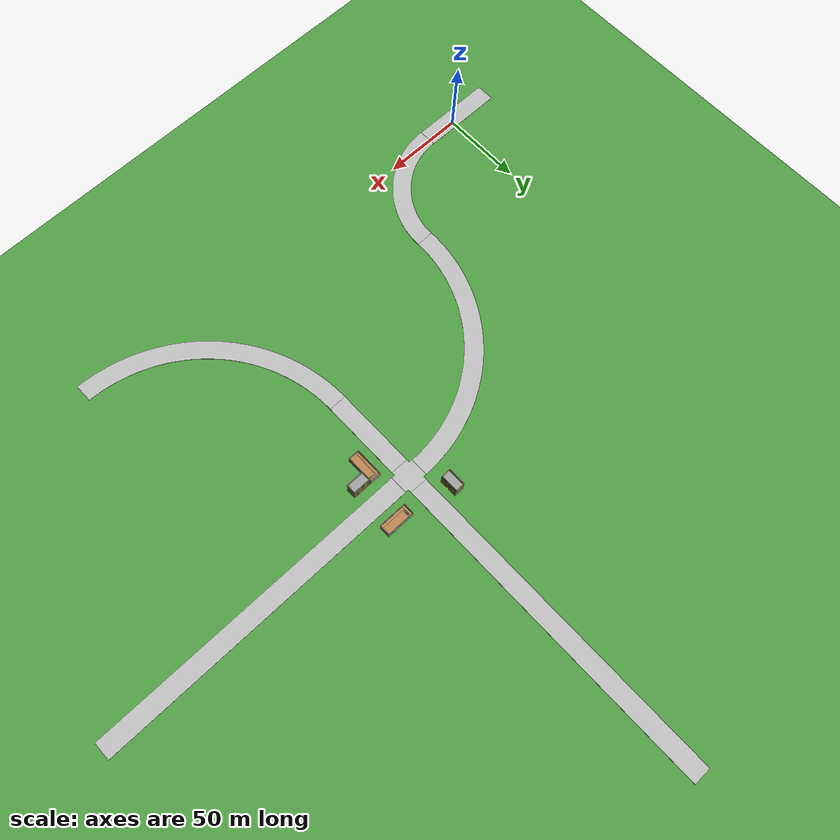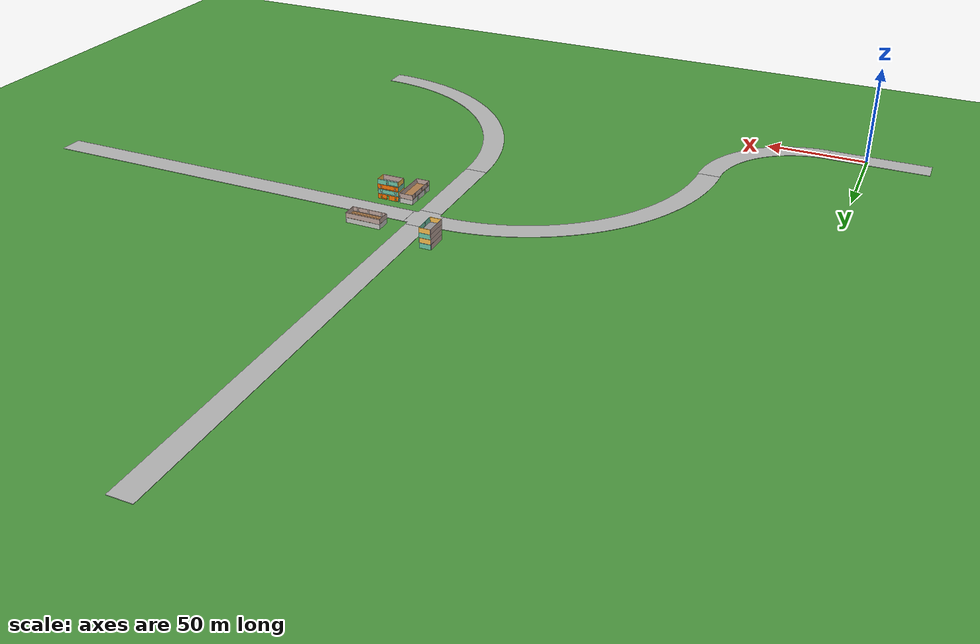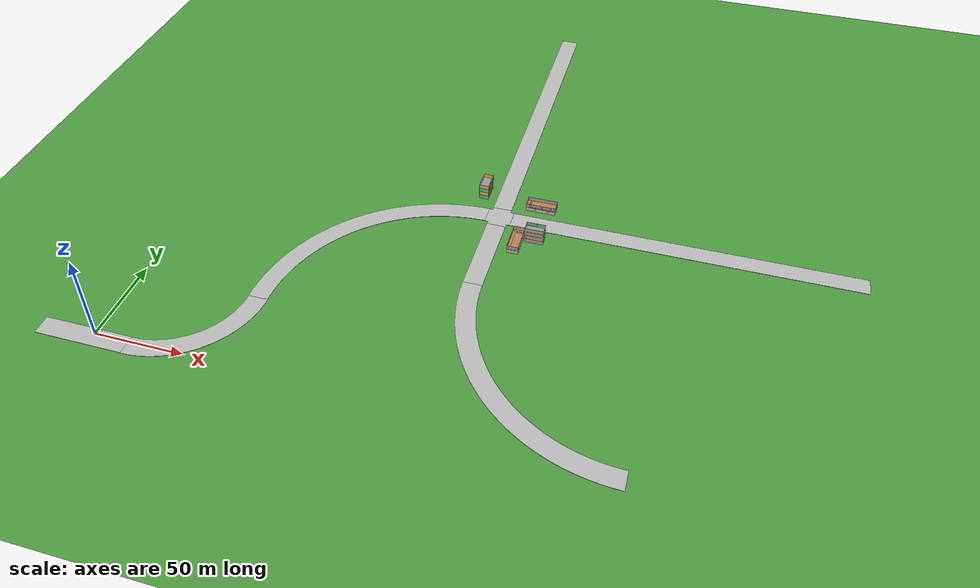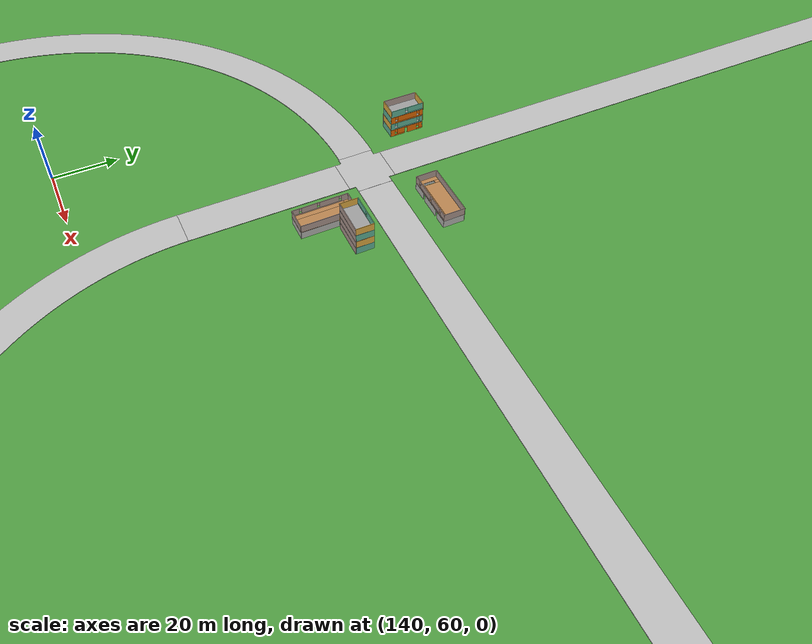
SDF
<sdf version="1.4">
 <world name="default">
  <light name="sun" type="directional">
   <pose>0 0 10 0 -0 0</pose>
   <diffuse>0.8 0.8 0.8 1</diffuse>
   <specular>0.2 0.2 0.2 1</specular>
   <attenuation>
    <range>10000</range>
    <constant>0.9</constant>
    <linear>0.01</linear>
    <quadratic>0.001</quadratic>
   </attenuation>
   <direction>0 0 -1</direction>
  </light>
  <model name="ground_plane">
   <static>1</static>
   <link name="link">
    <collision name="collision">
     <geometry><plane><normal>0 0 1</normal><size>10000 10000</size></plane></geometry>
     <surface><friction><ode><mu>100</mu><mu2>50</mu2></ode></friction></surface>
    </collision>
    <visual name="visual">
     <cast_shadows>0</cast_shadows>
     <geometry><plane><normal>0 0 1</normal><size>10000 10000</size></plane></geometry>
     <material>
      <script>
       <uri>model://grass_background/materials/scripts</uri>
       <uri>model://grass_background/materials/textures</uri>
       <name>GrassBackground</name>
      </script>
     </material>
    </visual>
    <velocity_decay><linear>0</linear><angular>0</angular></velocity_decay>
   </link>
  </model>
  <physics type="ode">
   <max_step_size>0.001</max_step_size>
   <real_time_factor>1</real_time_factor>
   <real_time_update_rate>1000</real_time_update_rate>
   <gravity>0 0 -9.8</gravity>
  </physics>
  <scene>
   <ambient>0.4 0.4 0.4 1</ambient>
   <background>0 0.9 0.9 1</background>
   <shadows>1</shadows>
   <grid>0</grid>
  </scene>
  <spherical_coordinates>
   <surface_model>EARTH_WGS84</surface_model>
   <latitude_deg>0</latitude_deg>
   <longitude_deg>0</longitude_deg>
   <elevation>0</elevation>
   <heading_deg>0</heading_deg>
  </spherical_coordinates>
  <model name="Straight Road - 50m">
   <static>1</static>
   <link name="link">
    <inertial>
     <mass>1</mass>
     <inertia><ixx>1</ixx><iyy>1</iyy><izz>1</izz><ixy>0</ixy><ixz>0</ixz><iyz>0</iyz></inertia>
    </inertial>
    <collision name="collision">
     <geometry><mesh><uri>model://straight_road_50m/meshes/straight_road_50m.dae</uri></mesh></geometry>
    </collision>
    <visual name="visual">
     <geometry><mesh><uri>model://straight_road_50m/meshes/straight_road_50m.dae</uri></mesh></geometry>
    </visual>
    <velocity_decay><linear>0</linear><angular>0</angular></velocity_decay>
   </link>
   <pose>-5.91467 7.68114 0 0 -0 0</pose>
  </model>
  <model name="Curved Road - 50m">
   <static>1</static>
   <link name="link">
    <inertial>
     <mass>1</mass>
     <inertia><ixx>1</ixx><iyy>1</iyy><izz>1</izz><ixy>0</ixy><ixz>0</ixz><iyz>0</iyz></inertia>
    </inertial>
    <collision name="collision">
     <geometry><mesh><uri>model://curved_road_50m/meshes/curved_road_50m.dae</uri></mesh></geometry>
    </collision>
    <visual name="visual">
     <geometry><mesh><uri>model://curved_road_50m/meshes/curved_road_50m.dae</uri></mesh></geometry>
    </visual>
    <velocity_decay><linear>0</linear><angular>0</angular></velocity_decay>
   </link>
   <pose>46.8363 19.7304 0 0 -0 0</pose>
  </model>
  <model name="Curved Road - 100m">
   <static>1</static>
   <link name="link">
    <inertial>
     <mass>1</mass>
     <inertia><ixx>1</ixx><iyy>1</iyy><izz>1</izz><ixy>0</ixy><ixz>0</ixz><iyz>0</iyz></inertia>
    </inertial>
    <collision name="collision">
     <geometry><mesh><uri>model://curved_road_100m/meshes/curved_road_100m.dae</uri></mesh></geometry>
    </collision>
    <visual name="visual">
     <geometry><mesh><uri>model://curved_road_100m/meshes/curved_road_100m.dae</uri></mesh></geometry>
    </visual>
    <velocity_decay><linear>0</linear><angular>0</angular></velocity_decay>
   </link>
   <pose>116.082 99.8936 0 0 0 -3.141</pose>
  </model>
  <model name="Straight Road - 200m">
   <static>1</static>
   <link name="link">
    <inertial>
     <mass>1</mass>
     <inertia><ixx>1</ixx><iyy>1</iyy><izz>1</izz><ixy>0</ixy><ixz>0</ixz><iyz>0</iyz></inertia>
    </inertial>
    <collision name="collision">
     <geometry><mesh><uri>model://straight_road_200m/meshes/straight_road_200m.dae</uri></mesh></geometry>
    </collision>
    <visual name="visual">
     <geometry><mesh><uri>model://straight_road_200m/meshes/straight_road_200m.dae</uri></mesh></geometry>
    </visual>
    <velocity_decay><linear>0</linear><angular>0</angular></velocity_decay>
   </link>
   <pose>283.793 137.123 0 0 0 -3.14069</pose>
  </model>
  <model name="Intersection">
   <static>1</static>
   <link name="link">
    <inertial>
     <mass>1</mass>
     <inertia><ixx>1</ixx><iyy>1</iyy><izz>1</izz><ixy>0</ixy><ixz>0</ixz><iyz>0</iyz></inertia>
    </inertial>
    <collision name="collision">
     <geometry><mesh><uri>model://intersection/meshes/intersection.dae</uri></mesh></geometry>
    </collision>
    <visual name="visual">
     <geometry><mesh><uri>model://intersection/meshes/intersection.dae</uri></mesh></geometry>
    </visual>
   </link>
   <pose>176.235 147 0 0 -0 0.000902</pose>
  </model>
  <model name="Straight Road - 50m_0">
   <static>1</static>
   <link name="link">
    <inertial>
     <mass>1</mass>
     <inertia><ixx>1</ixx><iyy>1</iyy><izz>1</izz><ixy>0</ixy><ixz>0</ixz><iyz>0</iyz></inertia>
    </inertial>
    <collision name="collision">
     <geometry><mesh><uri>model://straight_road_50m/meshes/straight_road_50m.dae</uri></mesh></geometry>
    </collision>
    <visual name="visual">
     <geometry><mesh><uri>model://straight_road_50m/meshes/straight_road_50m.dae</uri></mesh></geometry>
    </visual>
   </link>
   <pose>166.219 114.517 0 0 -0 1.5707</pose>
  </model>
  <model name="Curved Road - 100m_0">
   <static>1</static>
   <link name="link">
    <inertial>
     <mass>1</mass>
     <inertia><ixx>1</ixx><iyy>1</iyy><izz>1</izz><ixy>0</ixy><ixz>0</ixz><iyz>0</iyz></inertia>
    </inertial>
    <collision name="collision">
     <geometry><mesh><uri>model://curved_road_100m/meshes/curved_road_100m.dae</uri></mesh></geometry>
    </collision>
    <visual name="visual">
     <geometry><mesh><uri>model://curved_road_100m/meshes/curved_road_100m.dae</uri></mesh></geometry>
    </visual>
   </link>
   <pose>223.466 36.8805 0 0 0 -1.5707</pose>
  </model>
  <model name="Straight Road - 200m_0">
   <static>1</static>
   <link name="link">
    <inertial>
     <mass>1</mass>
     <inertia><ixx>1</ixx><iyy>1</iyy><izz>1</izz><ixy>0</ixy><ixz>0</ixz><iyz>0</iyz></inertia>
    </inertial>
    <collision name="collision">
     <geometry><mesh><uri>model://straight_road_200m/meshes/straight_road_200m.dae</uri></mesh></geometry>
    </collision>
    <visual name="visual">
     <geometry><mesh><uri>model://straight_road_200m/meshes/straight_road_200m.dae</uri></mesh></geometry>
    </visual>
   </link>
   <pose>186.213 254.492 0 0 0 -1.57078</pose>
  </model>
  <model name="building1">
   <pose>198.425 160.803 0 0 -0 0</pose>
   <link name="Floor_0">
    <pose>-0 0 2.5 0 -0 0</pose>
    <visual name="Floor_0_Visual_0">
     <pose>-7.97619 0 0.05 0 -0 0</pose>
     <geometry><box><size>1.54762 6.75 0.1</size></box></geometry>
     <material>
      <script><uri>file://media/materials/scripts/gazebo.material</uri><name>Gazebo/Wood</name></script>
      <ambient>1 1 1 1</ambient>
     </material>
    </visual>
    <collision name="Floor_0_Collision_0">
     <geometry><box><size>1.54762 6.75 0.1</size></box></geometry>
     <pose>-7.97619 0 0.05 0 -0 0</pose>
    </collision>
    <visual name="Floor_0_Visual_1">
     <pose>0.77381 -2.54152 0.05 0 -0 0</pose>
     <geometry><box><size>15.9524 1.66697 0.1</size></box></geometry>
     <material>
      <script><uri>file://media/materials/scripts/gazebo.material</uri><name>Gazebo/Wood</name></script>
      <ambient>1 1 1 1</ambient>
     </material>
    </visual>
    <collision name="Floor_0_Collision_1">
     <geometry><box><size>15.9524 1.66697 0.1</size></box></geometry>
     <pose>0.77381 -2.54152 0.05 0 -0 0</pose>
    </collision>
    <visual name="Floor_0_Visual_2">
     <pose>1.27381 0.833484 0.05 0 -0 0</pose>
     <geometry><box><size>14.9524 5.08303 0.1</size></box></geometry>
     <material>
      <script><uri>file://media/materials/scripts/gazebo.material</uri><name>Gazebo/Wood</name></script>
      <ambient>1 1 1 1</ambient>
     </material>
    </visual>
    <collision name="Floor_0_Collision_2">
     <geometry><box><size>14.9524 5.08303 0.1</size></box></geometry>
     <pose>1.27381 0.833484 0.05 0 -0 0</pose>
    </collision>
    <visual name="Floor_0_Visual_3">
     <pose>-6.70238 2.58348 0.05 0 -0 0</pose>
     <geometry><box><size>1 1.58303 0.1</size></box></geometry>
     <material>
      <script><uri>file://media/materials/scripts/gazebo.material</uri><name>Gazebo/Wood</name></script>
      <ambient>1 1 1 1</ambient>
     </material>
    </visual>
    <collision name="Floor_0_Collision_3">
     <geometry><box><size>1 1.58303 0.1</size></box></geometry>
     <pose>-6.70238 2.58348 0.05 0 -0 0</pose>
    </collision>
   </link>
   <link name="Stairs_0">
    <visual name="Stairs_0_Visual_0">
     <pose>-6.70238 1.6753 0.083333 0 -0 0</pose>
     <geometry><box><size>1 0.233333 0.166667</size></box></geometry>
     <material>
      <script><uri>file://media/materials/scripts/gazebo.material</uri><name>Gazebo/CeilingTiled</name></script>
      <ambient>1 1 1 1</ambient>
     </material>
    </visual>
    <collision name="Stairs_0_Collision_0">
     <geometry><box><size>1 0.233333 0.166667</size></box></geometry>
     <pose>-6.70238 1.6753 0.083333 0 -0 0</pose>
    </collision>
    <visual name="Stairs_0_Visual_1">
     <pose>-6.70238 1.44197 0.25 0 -0 0</pose>
     <geometry><box><size>1 0.233335 0.166668</size></box></geometry>
     <material>
      <script><uri>file://media/materials/scripts/gazebo.material</uri><name>Gazebo/CeilingTiled</name></script>
      <ambient>1 1 1 1</ambient>
     </material>
    </visual>
    <collision name="Stairs_0_Collision_1">
     <geometry><box><size>1 0.233335 0.166668</size></box></geometry>
     <pose>-6.70238 1.44197 0.25 0 -0 0</pose>
    </collision>
    <visual name="Stairs_0_Visual_2">
     <pose>-6.70238 1.20863 0.416667 0 -0 0</pose>
     <geometry><box><size>1 0.233335 0.166668</size></box></geometry>
     <material>
      <script><uri>file://media/materials/scripts/gazebo.material</uri><name>Gazebo/CeilingTiled</name></script>
      <ambient>1 1 1 1</ambient>
     </material>
    </visual>
    <collision name="Stairs_0_Collision_2">
     <geometry><box><size>1 0.233335 0.166668</size></box></geometry>
     <pose>-6.70238 1.20863 0.416667 0 -0 0</pose>
    </collision>
    <visual name="Stairs_0_Visual_3">
     <pose>-6.70238 0.975302 0.583333 0 -0 0</pose>
     <geometry><box><size>1 0.233335 0.166668</size></box></geometry>
     <material>
      <script><uri>file://media/materials/scripts/gazebo.material</uri><name>Gazebo/CeilingTiled</name></script>
      <ambient>1 1 1 1</ambient>
     </material>
    </visual>
    <collision name="Stairs_0_Collision_3">
     <geometry><box><size>1 0.233335 0.166668</size></box></geometry>
     <pose>-6.70238 0.975302 0.583333 0 -0 0</pose>
    </collision>
    <visual name="Stairs_0_Visual_4">
     <pose>-6.70238 0.741969 0.75 0 -0 0</pose>
     <geometry><box><size>1 0.233335 0.166668</size></box></geometry>
     <material>
      <script><uri>file://media/materials/scripts/gazebo.material</uri><name>Gazebo/CeilingTiled</name></script>
      <ambient>1 1 1 1</ambient>
     </material>
    </visual>
    <collision name="Stairs_0_Collision_4">
     <geometry><box><size>1 0.233335 0.166668</size></box></geometry>
     <pose>-6.70238 0.741969 0.75 0 -0 0</pose>
    </collision>
    <visual name="Stairs_0_Visual_5">
     <pose>-6.70238 0.508635 0.916667 0 -0 0</pose>
     <geometry><box><size>1 0.233335 0.166668</size></box></geometry>
     <material>
      <script><uri>file://media/materials/scripts/gazebo.material</uri><name>Gazebo/CeilingTiled</name></script>
      <ambient>1 1 1 1</ambient>
     </material>
    </visual>
    <collision name="Stairs_0_Collision_5">
     <geometry><box><size>1 0.233335 0.166668</size></box></geometry>
     <pose>-6.70238 0.508635 0.916667 0 -0 0</pose>
    </collision>
    <visual name="Stairs_0_Visual_6">
     <pose>-6.70238 0.275302 1.08333 0 -0 0</pose>
     <geometry><box><size>1 0.233335 0.166668</size></box></geometry>
     <material>
      <script><uri>file://media/materials/scripts/gazebo.material</uri><name>Gazebo/CeilingTiled</name></script>
      <ambient>1 1 1 1</ambient>
     </material>
    </visual>
    <collision name="Stairs_0_Collision_6">
     <geometry><box><size>1 0.233335 0.166668</size></box></geometry>
     <pose>-6.70238 0.275302 1.08333 0 -0 0</pose>
    </collision>
    <visual name="Stairs_0_Visual_7">
     <pose>-6.70238 0.041969 1.25 0 -0 0</pose>
     <geometry><box><size>1 0.233335 0.166668</size></box></geometry>
     <material>
      <script><uri>file://media/materials/scripts/gazebo.material</uri><name>Gazebo/CeilingTiled</name></script>
      <ambient>1 1 1 1</ambient>
     </material>
    </visual>
    <collision name="Stairs_0_Collision_7">
     <geometry><box><size>1 0.233335 0.166668</size></box></geometry>
     <pose>-6.70238 0.041969 1.25 0 -0 0</pose>
    </collision>
    <visual name="Stairs_0_Visual_8">
     <pose>-6.70238 -0.191365 1.41667 0 -0 0</pose>
     <geometry><box><size>1 0.233335 0.166668</size></box></geometry>
     <material>
      <script><uri>file://media/materials/scripts/gazebo.material</uri><name>Gazebo/CeilingTiled</name></script>
      <ambient>1 1 1 1</ambient>
     </material>
    </visual>
    <collision name="Stairs_0_Collision_8">
     <geometry><box><size>1 0.233335 0.166668</size></box></geometry>
     <pose>-6.70238 -0.191365 1.41667 0 -0 0</pose>
    </collision>
    <visual name="Stairs_0_Visual_9">
     <pose>-6.70238 -0.424698 1.58333 0 -0 0</pose>
     <geometry><box><size>1 0.233335 0.166668</size></box></geometry>
     <material>
      <script><uri>file://media/materials/scripts/gazebo.material</uri><name>Gazebo/CeilingTiled</name></script>
      <ambient>1 1 1 1</ambient>
     </material>
    </visual>
    <collision name="Stairs_0_Collision_9">
     <geometry><box><size>1 0.233335 0.166668</size></box></geometry>
     <pose>-6.70238 -0.424698 1.58333 0 -0 0</pose>
    </collision>
    <visual name="Stairs_0_Visual_10">
     <pose>-6.70238 -0.658031 1.75 0 -0 0</pose>
     <geometry><box><size>1 0.233335 0.166668</size></box></geometry>
     <material>
      <script><uri>file://media/materials/scripts/gazebo.material</uri><name>Gazebo/CeilingTiled</name></script>
      <ambient>1 1 1 1</ambient>
     </material>
    </visual>
    <collision name="Stairs_0_Collision_10">
     <geometry><box><size>1 0.233335 0.166668</size></box></geometry>
     <pose>-6.70238 -0.658031 1.75 0 -0 0</pose>
    </collision>
    <visual name="Stairs_0_Visual_11">
     <pose>-6.70238 -0.891365 1.91667 0 -0 0</pose>
     <geometry><box><size>1 0.233335 0.166668</size></box></geometry>
     <material>
      <script><uri>file://media/materials/scripts/gazebo.material</uri><name>Gazebo/CeilingTiled</name></script>
      <ambient>1 1 1 1</ambient>
     </material>
    </visual>
    <collision name="Stairs_0_Collision_11">
     <geometry><box><size>1 0.233335 0.166668</size></box></geometry>
     <pose>-6.70238 -0.891365 1.91667 0 -0 0</pose>
    </collision>
    <visual name="Stairs_0_Visual_12">
     <pose>-6.70238 -1.1247 2.08333 0 -0 0</pose>
     <geometry><box><size>1 0.233335 0.166668</size></box></geometry>
     <material>
      <script><uri>file://media/materials/scripts/gazebo.material</uri><name>Gazebo/CeilingTiled</name></script>
      <ambient>1 1 1 1</ambient>
     </material>
    </visual>
    <collision name="Stairs_0_Collision_12">
     <geometry><box><size>1 0.233335 0.166668</size></box></geometry>
     <pose>-6.70238 -1.1247 2.08333 0 -0 0</pose>
    </collision>
    <visual name="Stairs_0_Visual_13">
     <pose>-6.70238 -1.35803 2.25 0 -0 0</pose>
     <geometry><box><size>1 0.233335 0.166668</size></box></geometry>
     <material>
      <script><uri>file://media/materials/scripts/gazebo.material</uri><name>Gazebo/CeilingTiled</name></script>
      <ambient>1 1 1 1</ambient>
     </material>
    </visual>
    <collision name="Stairs_0_Collision_13">
     <geometry><box><size>1 0.233335 0.166668</size></box></geometry>
     <pose>-6.70238 -1.35803 2.25 0 -0 0</pose>
    </collision>
    <visual name="Stairs_0_Visual_14">
     <pose>-6.70238 -1.59136 2.41667 0 -0 0</pose>
     <geometry><box><size>1 0.233335 0.166668</size></box></geometry>
     <material>
      <script><uri>file://media/materials/scripts/gazebo.material</uri><name>Gazebo/CeilingTiled</name></script>
      <ambient>1 1 1 1</ambient>
     </material>
    </visual>
    <collision name="Stairs_0_Collision_14">
     <geometry><box><size>1 0.233335 0.166668</size></box></geometry>
     <pose>-6.70238 -1.59136 2.41667 0 -0 0</pose>
    </collision>
   </link>
   <link name="Wall_0">
    <pose>-0 -3.3 0 0 -0 0</pose>
    <visual name="Wall_0_Visual_0">
     <pose>-6.25056 0 1.25 0 -0 0</pose>
     <geometry><box><size>4.99888 0.15 2.5</size></box></geometry>
     <material>
      <script><uri>file://media/materials/scripts/gazebo.material</uri><name>Gazebo/CeilingTiled</name></script>
      <ambient>1 1 1 1</ambient>
     </material>
    </visual>
    <collision name="Wall_0_Collision_0">
     <geometry><box><size>4.99888 0.15 2.5</size></box></geometry>
     <pose>-6.25056 0 1.25 0 -0 0</pose>
    </collision>
    <visual name="Wall_0_Visual_1">
     <pose>0.460751 0 1.25 0 -0 0</pose>
     <geometry><box><size>6.62374 0.15 2.5</size></box></geometry>
     <material>
      <script><uri>file://media/materials/scripts/gazebo.material</uri><name>Gazebo/CeilingTiled</name></script>
      <ambient>1 1 1 1</ambient>
     </material>
    </visual>
    <collision name="Wall_0_Collision_1">
     <geometry><box><size>6.62374 0.15 2.5</size></box></geometry>
     <pose>0.460751 0 1.25 0 -0 0</pose>
    </collision>
    <visual name="Wall_0_Visual_2">
     <pose>6.71131 0 1.25 0 -0 0</pose>
     <geometry><box><size>4.07738 0.15 2.5</size></box></geometry>
     <material>
      <script><uri>file://media/materials/scripts/gazebo.material</uri><name>Gazebo/CeilingTiled</name></script>
      <ambient>1 1 1 1</ambient>
     </material>
    </visual>
    <collision name="Wall_0_Collision_2">
     <geometry><box><size>4.07738 0.15 2.5</size></box></geometry>
     <pose>6.71131 0 1.25 0 -0 0</pose>
    </collision>
    <visual name="Wall_0_Visual_3">
     <pose>-3.30112 0 2.25 0 -0 0</pose>
     <geometry><box><size>0.9 0.15 0.5</size></box></geometry>
     <material>
      <script><uri>file://media/materials/scripts/gazebo.material</uri><name>Gazebo/CeilingTiled</name></script>
      <ambient>1 1 1 1</ambient>
     </material>
    </visual>
    <collision name="Wall_0_Collision_3">
     <geometry><box><size>0.9 0.15 0.5</size></box></geometry>
     <pose>-3.30112 0 2.25 0 -0 0</pose>
    </collision>
    <visual name="Wall_0_Visual_4">
     <pose>4.22262 0 2.25 0 -0 0</pose>
     <geometry><box><size>0.9 0.15 0.5</size></box></geometry>
     <material>
      <script><uri>file://media/materials/scripts/gazebo.material</uri><name>Gazebo/CeilingTiled</name></script>
      <ambient>1 1 1 1</ambient>
     </material>
    </visual>
    <collision name="Wall_0_Collision_4">
     <geometry><box><size>0.9 0.15 0.5</size></box></geometry>
     <pose>4.22262 0 2.25 0 -0 0</pose>
    </collision>
   </link>
   <link name="Wall_1">
    <collision name="Wall_1_Collision">
     <geometry><box><size>6.75 0.15 2.5</size></box></geometry>
     <pose>0 0 1.25 0 -0 0</pose>
    </collision>
    <visual name="Wall_1_Visual">
     <pose>0 0 1.25 0 -0 0</pose>
     <geometry><box><size>6.75 0.15 2.5</size></box></geometry>
     <material>
      <script><uri>file://media/materials/scripts/gazebo.material</uri><name>Gazebo/CeilingTiled</name></script>
      <ambient>1 1 1 1</ambient>
     </material>
    </visual>
    <pose>8.675 0 0 0 -0 1.5708</pose>
   </link>
   <link name="Wall_2">
    <collision name="Wall_2_Collision">
     <geometry><box><size>17.5 0.15 2.5</size></box></geometry>
     <pose>0 0 1.25 0 -0 0</pose>
    </collision>
    <visual name="Wall_2_Visual">
     <pose>0 0 1.25 0 -0 0</pose>
     <geometry><box><size>17.5 0.15 2.5</size></box></geometry>
     <material>
      <script><uri>file://media/materials/scripts/gazebo.material</uri><name>Gazebo/CeilingTiled</name></script>
      <ambient>1 1 1 1</ambient>
     </material>
    </visual>
    <pose>-0 3.3 0 0 -0 3.14159</pose>
   </link>
   <link name="Wall_3">
    <collision name="Wall_3_Collision">
     <geometry><box><size>6.75 0.15 2.5</size></box></geometry>
     <pose>0 0 1.25 0 -0 0</pose>
    </collision>
    <visual name="Wall_3_Visual">
     <pose>0 0 1.25 0 -0 0</pose>
     <geometry><box><size>6.75 0.15 2.5</size></box></geometry>
     <material>
      <script><uri>file://media/materials/scripts/gazebo.material</uri><name>Gazebo/CeilingTiled</name></script>
      <ambient>1 1 1 1</ambient>
     </material>
    </visual>
    <pose>-8.675 0 0 0 0 -1.5708</pose>
   </link>
   <link name="Wall_5">
    <pose>-0 -3.3 2.5 0 -0 0</pose>
    <visual name="Wall_5_Visual_0">
     <pose>-7.69619 0 1.25 0 -0 0</pose>
     <geometry><box><size>2.10762 0.15 2.5</size></box></geometry>
     <material>
      <script><uri>file://media/materials/scripts/gazebo.material</uri><name>Gazebo/Grey</name></script>
      <ambient>0.760784 0.662745 0.627451 1</ambient>
     </material>
    </visual>
    <collision name="Wall_5_Collision_0">
     <geometry><box><size>2.10762 0.15 2.5</size></box></geometry>
     <pose>-7.69619 0 1.25 0 -0 0</pose>
    </collision>
    <visual name="Wall_5_Visual_1">
     <pose>1.05381 0 0.25 0 -0 0</pose>
     <geometry><box><size>15.3924 0.15 0.5</size></box></geometry>
     <material>
      <script><uri>file://media/materials/scripts/gazebo.material</uri><name>Gazebo/Grey</name></script>
      <ambient>0.760784 0.662745 0.627451 1</ambient>
     </material>
    </visual>
    <collision name="Wall_5_Collision_1">
     <geometry><box><size>15.3924 0.15 0.5</size></box></geometry>
     <pose>1.05381 0 0.25 0 -0 0</pose>
    </collision>
    <visual name="Wall_5_Visual_2">
     <pose>-2.82688 0 1.5 0 -0 0</pose>
     <geometry><box><size>6.031 0.15 2</size></box></geometry>
     <material>
      <script><uri>file://media/materials/scripts/gazebo.material</uri><name>Gazebo/Grey</name></script>
      <ambient>0.760784 0.662745 0.627451 1</ambient>
     </material>
    </visual>
    <collision name="Wall_5_Collision_2">
     <geometry><box><size>6.031 0.15 2</size></box></geometry>
     <pose>-2.82688 0 1.5 0 -0 0</pose>
    </collision>
    <visual name="Wall_5_Visual_3">
     <pose>3.36012 0 1.5 0 -0 0</pose>
     <geometry><box><size>4.743 0.15 2</size></box></geometry>
     <material>
      <script><uri>file://media/materials/scripts/gazebo.material</uri><name>Gazebo/Grey</name></script>
      <ambient>0.760784 0.662745 0.627451 1</ambient>
     </material>
    </visual>
    <collision name="Wall_5_Collision_3">
     <geometry><box><size>4.743 0.15 2</size></box></geometry>
     <pose>3.36012 0 1.5 0 -0 0</pose>
    </collision>
    <visual name="Wall_5_Visual_4">
     <pose>7.64081 0 1.5 0 -0 0</pose>
     <geometry><box><size>2.21838 0.15 2</size></box></geometry>
     <material>
      <script><uri>file://media/materials/scripts/gazebo.material</uri><name>Gazebo/Grey</name></script>
      <ambient>0.760784 0.662745 0.627451 1</ambient>
     </material>
    </visual>
    <collision name="Wall_5_Collision_4">
     <geometry><box><size>2.21838 0.15 2</size></box></geometry>
     <pose>7.64081 0 1.5 0 -0 0</pose>
    </collision>
    <visual name="Wall_5_Visual_5">
     <pose>-6.24238 0 1.9 0 -0 0</pose>
     <geometry><box><size>0.8 0.15 1.2</size></box></geometry>
     <material>
      <script><uri>file://media/materials/scripts/gazebo.material</uri><name>Gazebo/Grey</name></script>
      <ambient>0.760784 0.662745 0.627451 1</ambient>
     </material>
    </visual>
    <collision name="Wall_5_Collision_5">
     <geometry><box><size>0.8 0.15 1.2</size></box></geometry>
     <pose>-6.24238 0 1.9 0 -0 0</pose>
    </collision>
    <visual name="Wall_5_Visual_6">
     <pose>0.588621 0 1.9 0 -0 0</pose>
     <geometry><box><size>0.8 0.15 1.2</size></box></geometry>
     <material>
      <script><uri>file://media/materials/scripts/gazebo.material</uri><name>Gazebo/Grey</name></script>
      <ambient>0.760784 0.662745 0.627451 1</ambient>
     </material>
    </visual>
    <collision name="Wall_5_Collision_6">
     <geometry><box><size>0.8 0.15 1.2</size></box></geometry>
     <pose>0.588621 0 1.9 0 -0 0</pose>
    </collision>
    <visual name="Wall_5_Visual_7">
     <pose>6.13162 0 1.9 0 -0 0</pose>
     <geometry><box><size>0.8 0.15 1.2</size></box></geometry>
     <material>
      <script><uri>file://media/materials/scripts/gazebo.material</uri><name>Gazebo/Grey</name></script>
      <ambient>0.760784 0.662745 0.627451 1</ambient>
     </material>
    </visual>
    <collision name="Wall_5_Collision_7">
     <geometry><box><size>0.8 0.15 1.2</size></box></geometry>
     <pose>6.13162 0 1.9 0 -0 0</pose>
    </collision>
   </link>
   <link name="Wall_6">
    <collision name="Wall_6_Collision">
     <geometry><box><size>6.75 0.15 2.5</size></box></geometry>
     <pose>0 0 1.25 0 -0 0</pose>
    </collision>
    <visual name="Wall_6_Visual">
     <pose>0 0 1.25 0 -0 0</pose>
     <geometry><box><size>6.75 0.15 2.5</size></box></geometry>
     <material>
      <script><uri>file://media/materials/scripts/gazebo.material</uri><name>Gazebo/Grey</name></script>
      <ambient>0.760784 0.662745 0.627451 1</ambient>
     </material>
    </visual>
    <pose>8.675 0 2.5 0 -0 1.5708</pose>
   </link>
   <link name="Wall_7">
    <collision name="Wall_7_Collision">
     <geometry><box><size>17.5 0.15 2.5</size></box></geometry>
     <pose>0 0 1.25 0 -0 0</pose>
    </collision>
    <visual name="Wall_7_Visual">
     <pose>0 0 1.25 0 -0 0</pose>
     <geometry><box><size>17.5 0.15 2.5</size></box></geometry>
     <material>
      <script><uri>file://media/materials/scripts/gazebo.material</uri><name>Gazebo/Grey</name></script>
      <ambient>0.760784 0.662745 0.627451 1</ambient>
     </material>
    </visual>
    <pose>-0 3.3 2.5 0 -0 3.14159</pose>
   </link>
   <link name="Wall_8">
    <collision name="Wall_8_Collision">
     <geometry><box><size>6.75 0.15 2.5</size></box></geometry>
     <pose>0 0 1.25 0 -0 0</pose>
    </collision>
    <visual name="Wall_8_Visual">
     <pose>0 0 1.25 0 -0 0</pose>
     <geometry><box><size>6.75 0.15 2.5</size></box></geometry>
     <material>
      <script><uri>file://media/materials/scripts/gazebo.material</uri><name>Gazebo/Grey</name></script>
      <ambient>0.760784 0.662745 0.627451 1</ambient>
     </material>
    </visual>
    <pose>-8.675 0 2.5 0 0 -1.5708</pose>
   </link>
   <static>1</static>
  </model>
  <model name="building2">
   <pose>200.516 133.366 0 0 -0 3.14159</pose>
   <link name="Floor_1">
    <collision name="Floor_1_Collision">
     <geometry><box><size>11 5.75 0.1</size></box></geometry>
     <pose>0 0 0.05 0 -0 0</pose>
    </collision>
    <visual name="Floor_1_Visual">
     <pose>0 0 0.05 0 -0 0</pose>
     <geometry><box><size>11 5.75 0.1</size></box></geometry>
     <material>
      <script><uri>file://media/materials/scripts/gazebo.material</uri><name>Gazebo/Grey</name></script>
      <ambient>1 1 1 1</ambient>
     </material>
    </visual>
    <pose>-0 0 2.5 0 -0 0</pose>
   </link>
   <link name="Floor_2">
    <collision name="Floor_2_Collision">
     <geometry><box><size>11 5.75 0.1</size></box></geometry>
     <pose>0 0 0.05 0 -0 0</pose>
    </collision>
    <visual name="Floor_2_Visual">
     <pose>0 0 0.05 0 -0 0</pose>
     <geometry><box><size>11 5.75 0.1</size></box></geometry>
     <material>
      <script><uri>file://media/materials/scripts/gazebo.material</uri><name>Gazebo/Grey</name></script>
      <ambient>1 1 1 1</ambient>
     </material>
    </visual>
    <pose>-0 0 5 0 -0 0</pose>
   </link>
   <link name="Floor_3">
    <collision name="Floor_3_Collision">
     <geometry><box><size>11 5.75 0.1</size></box></geometry>
     <pose>0 0 0.05 0 -0 0</pose>
    </collision>
    <visual name="Floor_3_Visual">
     <pose>0 0 0.05 0 -0 0</pose>
     <geometry><box><size>11 5.75 0.1</size></box></geometry>
     <material>
      <script><uri>file://media/materials/scripts/gazebo.material</uri><name>Gazebo/Grey</name></script>
      <ambient>1 1 1 1</ambient>
     </material>
    </visual>
    <pose>-0 0 7.5 0 -0 0</pose>
   </link>
   <link name="Wall_10">
    <collision name="Wall_10_Collision">
     <geometry><box><size>5.75 0.15 2.5</size></box></geometry>
     <pose>0 0 1.25 0 -0 0</pose>
    </collision>
    <visual name="Wall_10_Visual">
     <pose>0 0 1.25 0 -0 0</pose>
     <geometry><box><size>5.75 0.15 2.5</size></box></geometry>
     <material>
      <script><uri>file://media/materials/scripts/gazebo.material</uri><name>Gazebo/Grey</name></script>
      <ambient>0.435294 0.796078 0.67451 1</ambient>
     </material>
    </visual>
    <pose>5.425 0 0 0 -0 1.5708</pose>
   </link>
   <link name="Wall_11">
    <collision name="Wall_11_Collision">
     <geometry><box><size>11 0.15 2.5</size></box></geometry>
     <pose>0 0 1.25 0 -0 0</pose>
    </collision>
    <visual name="Wall_11_Visual">
     <pose>0 0 1.25 0 -0 0</pose>
     <geometry><box><size>11 0.15 2.5</size></box></geometry>
     <material>
      <script><uri>file://media/materials/scripts/gazebo.material</uri><name>Gazebo/Grey</name></script>
      <ambient>0.760784 0.662745 0.627451 1</ambient>
     </material>
    </visual>
    <pose>-0 2.8 0 0 -0 3.14159</pose>
   </link>
   <link name="Wall_12">
    <collision name="Wall_12_Collision">
     <geometry><box><size>5.75 0.15 2.5</size></box></geometry>
     <pose>0 0 1.25 0 -0 0</pose>
    </collision>
    <visual name="Wall_12_Visual">
     <pose>0 0 1.25 0 -0 0</pose>
     <geometry><box><size>5.75 0.15 2.5</size></box></geometry>
     <material>
      <script><uri>file://media/materials/scripts/gazebo.material</uri><name>Gazebo/Grey</name></script>
      <ambient>0.435294 0.796078 0.67451 1</ambient>
     </material>
    </visual>
    <pose>-5.425 0 0 0 0 -1.5708</pose>
   </link>
   <link name="Wall_14">
    <pose>-0 -2.8 2.5 0 -0 0</pose>
    <visual name="Wall_14_Visual_0">
     <pose>-4.78604 0 1.25 0 -0 0</pose>
     <geometry><box><size>1.42793 0.15 2.5</size></box></geometry>
     <material>
      <script><uri>file://media/materials/scripts/gazebo.material</uri><name>Gazebo/Grey</name></script>
      <ambient>0.435294 0.796078 0.67451 1</ambient>
     </material>
    </visual>
    <collision name="Wall_14_Collision_0">
     <geometry><box><size>1.42793 0.15 2.5</size></box></geometry>
     <pose>-4.78604 0 1.25 0 -0 0</pose>
    </collision>
    <visual name="Wall_14_Visual_1">
     <pose>0.713965 0 0.25 0 -0 0</pose>
     <geometry><box><size>9.57207 0.15 0.5</size></box></geometry>
     <material>
      <script><uri>file://media/materials/scripts/gazebo.material</uri><name>Gazebo/Grey</name></script>
      <ambient>0.435294 0.796078 0.67451 1</ambient>
     </material>
    </visual>
    <collision name="Wall_14_Collision_1">
     <geometry><box><size>9.57207 0.15 0.5</size></box></geometry>
     <pose>0.713965 0 0.25 0 -0 0</pose>
    </collision>
    <visual name="Wall_14_Visual_2">
     <pose>0.069283 0 1.5 0 -0 0</pose>
     <geometry><box><size>6.68271 0.15 2</size></box></geometry>
     <material>
      <script><uri>file://media/materials/scripts/gazebo.material</uri><name>Gazebo/Grey</name></script>
      <ambient>0.435294 0.796078 0.67451 1</ambient>
     </material>
    </visual>
    <collision name="Wall_14_Collision_2">
     <geometry><box><size>6.68271 0.15 2</size></box></geometry>
     <pose>0.069283 0 1.5 0 -0 0</pose>
    </collision>
    <visual name="Wall_14_Visual_3">
     <pose>4.85532 0 1.5 0 -0 0</pose>
     <geometry><box><size>1.28937 0.15 2</size></box></geometry>
     <material>
      <script><uri>file://media/materials/scripts/gazebo.material</uri><name>Gazebo/Grey</name></script>
      <ambient>0.435294 0.796078 0.67451 1</ambient>
     </material>
    </visual>
    <collision name="Wall_14_Collision_3">
     <geometry><box><size>1.28937 0.15 2</size></box></geometry>
     <pose>4.85532 0 1.5 0 -0 0</pose>
    </collision>
    <visual name="Wall_14_Visual_4">
     <pose>-3.67207 0 1.9 0 -0 0</pose>
     <geometry><box><size>0.8 0.15 1.2</size></box></geometry>
     <material>
      <script><uri>file://media/materials/scripts/gazebo.material</uri><name>Gazebo/Grey</name></script>
      <ambient>0.435294 0.796078 0.67451 1</ambient>
     </material>
    </visual>
    <collision name="Wall_14_Collision_4">
     <geometry><box><size>0.8 0.15 1.2</size></box></geometry>
     <pose>-3.67207 0 1.9 0 -0 0</pose>
    </collision>
    <visual name="Wall_14_Visual_5">
     <pose>3.81063 0 1.9 0 -0 0</pose>
     <geometry><box><size>0.8 0.15 1.2</size></box></geometry>
     <material>
      <script><uri>file://media/materials/scripts/gazebo.material</uri><name>Gazebo/Grey</name></script>
      <ambient>0.435294 0.796078 0.67451 1</ambient>
     </material>
    </visual>
    <collision name="Wall_14_Collision_5">
     <geometry><box><size>0.8 0.15 1.2</size></box></geometry>
     <pose>3.81063 0 1.9 0 -0 0</pose>
    </collision>
   </link>
   <link name="Wall_15">
    <collision name="Wall_15_Collision">
     <geometry><box><size>5.75 0.15 2.5</size></box></geometry>
     <pose>0 0 1.25 0 -0 0</pose>
    </collision>
    <visual name="Wall_15_Visual">
     <pose>0 0 1.25 0 -0 0</pose>
     <geometry><box><size>5.75 0.15 2.5</size></box></geometry>
     <material>
      <script><uri>file://media/materials/scripts/gazebo.material</uri><name>Gazebo/Grey</name></script>
      <ambient>1 0.764706 0.305882 1</ambient>
     </material>
    </visual>
    <pose>5.425 0 2.5 0 -0 1.5708</pose>
   </link>
   <link name="Wall_16">
    <collision name="Wall_16_Collision">
     <geometry><box><size>11 0.15 2.5</size></box></geometry>
     <pose>0 0 1.25 0 -0 0</pose>
    </collision>
    <visual name="Wall_16_Visual">
     <pose>0 0 1.25 0 -0 0</pose>
     <geometry><box><size>11 0.15 2.5</size></box></geometry>
     <material>
      <script><uri>file://media/materials/scripts/gazebo.material</uri><name>Gazebo/Grey</name></script>
      <ambient>0.760784 0.662745 0.627451 1</ambient>
     </material>
    </visual>
    <pose>-0 2.8 2.5 0 -0 3.14159</pose>
   </link>
   <link name="Wall_17">
    <collision name="Wall_17_Collision">
     <geometry><box><size>5.75 0.15 2.5</size></box></geometry>
     <pose>0 0 1.25 0 -0 0</pose>
    </collision>
    <visual name="Wall_17_Visual">
     <pose>0 0 1.25 0 -0 0</pose>
     <geometry><box><size>5.75 0.15 2.5</size></box></geometry>
     <material>
      <script><uri>file://media/materials/scripts/gazebo.material</uri><name>Gazebo/Grey</name></script>
      <ambient>1 0.764706 0.305882 1</ambient>
     </material>
    </visual>
    <pose>-5.425 0 2.5 0 0 -1.5708</pose>
   </link>
   <link name="Wall_18">
    <pose>-0 -2.8 5 0 -0 0</pose>
    <visual name="Wall_18_Visual_0">
     <pose>-4.78604 0 1.25 0 -0 0</pose>
     <geometry><box><size>1.42793 0.15 2.5</size></box></geometry>
     <material>
      <script><uri>file://media/materials/scripts/gazebo.material</uri><name>Gazebo/Grey</name></script>
      <ambient>0.996078 0.47451 0.0196078 1</ambient>
     </material>
    </visual>
    <collision name="Wall_18_Collision_0">
     <geometry><box><size>1.42793 0.15 2.5</size></box></geometry>
     <pose>-4.78604 0 1.25 0 -0 0</pose>
    </collision>
    <visual name="Wall_18_Visual_1">
     <pose>0.713965 0 0.25 0 -0 0</pose>
     <geometry><box><size>9.57207 0.15 0.5</size></box></geometry>
     <material>
      <script><uri>file://media/materials/scripts/gazebo.material</uri><name>Gazebo/Grey</name></script>
      <ambient>0.996078 0.47451 0.0196078 1</ambient>
     </material>
    </visual>
    <collision name="Wall_18_Collision_1">
     <geometry><box><size>9.57207 0.15 0.5</size></box></geometry>
     <pose>0.713965 0 0.25 0 -0 0</pose>
    </collision>
    <visual name="Wall_18_Visual_2">
     <pose>0.038865 0 1.5 0 -0 0</pose>
     <geometry><box><size>6.62187 0.15 2</size></box></geometry>
     <material>
      <script><uri>file://media/materials/scripts/gazebo.material</uri><name>Gazebo/Grey</name></script>
      <ambient>0.996078 0.47451 0.0196078 1</ambient>
     </material>
    </visual>
    <collision name="Wall_18_Collision_2">
     <geometry><box><size>6.62187 0.15 2</size></box></geometry>
     <pose>0.038865 0 1.5 0 -0 0</pose>
    </collision>
    <visual name="Wall_18_Visual_3">
     <pose>4.8249 0 1.5 0 -0 0</pose>
     <geometry><box><size>1.3502 0.15 2</size></box></geometry>
     <material>
      <script><uri>file://media/materials/scripts/gazebo.material</uri><name>Gazebo/Grey</name></script>
      <ambient>0.996078 0.47451 0.0196078 1</ambient>
     </material>
    </visual>
    <collision name="Wall_18_Collision_3">
     <geometry><box><size>1.3502 0.15 2</size></box></geometry>
     <pose>4.8249 0 1.5 0 -0 0</pose>
    </collision>
    <visual name="Wall_18_Visual_4">
     <pose>-3.67207 0 1.9 0 -0 0</pose>
     <geometry><box><size>0.8 0.15 1.2</size></box></geometry>
     <material>
      <script><uri>file://media/materials/scripts/gazebo.material</uri><name>Gazebo/Grey</name></script>
      <ambient>0.996078 0.47451 0.0196078 1</ambient>
     </material>
    </visual>
    <collision name="Wall_18_Collision_4">
     <geometry><box><size>0.8 0.15 1.2</size></box></geometry>
     <pose>-3.67207 0 1.9 0 -0 0</pose>
    </collision>
    <visual name="Wall_18_Visual_5">
     <pose>3.7498 0 1.9 0 -0 0</pose>
     <geometry><box><size>0.8 0.15 1.2</size></box></geometry>
     <material>
      <script><uri>file://media/materials/scripts/gazebo.material</uri><name>Gazebo/Grey</name></script>
      <ambient>0.996078 0.47451 0.0196078 1</ambient>
     </material>
    </visual>
    <collision name="Wall_18_Collision_5">
     <geometry><box><size>0.8 0.15 1.2</size></box></geometry>
     <pose>3.7498 0 1.9 0 -0 0</pose>
    </collision>
   </link>
   <link name="Wall_19">
    <collision name="Wall_19_Collision">
     <geometry><box><size>5.75 0.15 2.5</size></box></geometry>
     <pose>0 0 1.25 0 -0 0</pose>
    </collision>
    <visual name="Wall_19_Visual">
     <pose>0 0 1.25 0 -0 0</pose>
     <geometry><box><size>5.75 0.15 2.5</size></box></geometry>
     <material>
      <script><uri>file://media/materials/scripts/gazebo.material</uri><name>Gazebo/Grey</name></script>
      <ambient>0.435294 0.796078 0.67451 1</ambient>
     </material>
    </visual>
    <pose>5.425 0 5 0 -0 1.5708</pose>
   </link>
   <link name="Wall_20">
    <collision name="Wall_20_Collision">
     <geometry><box><size>11 0.15 2.5</size></box></geometry>
     <pose>0 0 1.25 0 -0 0</pose>
    </collision>
    <visual name="Wall_20_Visual">
     <pose>0 0 1.25 0 -0 0</pose>
     <geometry><box><size>11 0.15 2.5</size></box></geometry>
     <material>
      <script><uri>file://media/materials/scripts/gazebo.material</uri><name>Gazebo/Grey</name></script>
      <ambient>0.760784 0.662745 0.627451 1</ambient>
     </material>
    </visual>
    <pose>-0 2.8 5 0 -0 3.14159</pose>
   </link>
   <link name="Wall_21">
    <collision name="Wall_21_Collision">
     <geometry><box><size>5.75 0.15 2.5</size></box></geometry>
     <pose>0 0 1.25 0 -0 0</pose>
    </collision>
    <visual name="Wall_21_Visual">
     <pose>0 0 1.25 0 -0 0</pose>
     <geometry><box><size>5.75 0.15 2.5</size></box></geometry>
     <material>
      <script><uri>file://media/materials/scripts/gazebo.material</uri><name>Gazebo/Grey</name></script>
      <ambient>0.435294 0.796078 0.67451 1</ambient>
     </material>
    </visual>
    <pose>-5.425 0 5 0 0 -1.5708</pose>
   </link>
   <link name="Wall_22">
    <pose>-0 -2.8 7.5 0 -0 0</pose>
    <visual name="Wall_22_Visual_0">
     <pose>-3.09786 0 1.25 0 -0 0</pose>
     <geometry><box><size>4.80427 0.15 2.5</size></box></geometry>
     <material>
      <script><uri>file://media/materials/scripts/gazebo.material</uri><name>Gazebo/Grey</name></script>
      <ambient>0.435294 0.796078 0.67451 1</ambient>
     </material>
    </visual>
    <collision name="Wall_22_Collision_0">
     <geometry><box><size>4.80427 0.15 2.5</size></box></geometry>
     <pose>-3.09786 0 1.25 0 -0 0</pose>
    </collision>
    <visual name="Wall_22_Visual_1">
     <pose>2.40214 0 0.25 0 -0 0</pose>
     <geometry><box><size>6.19573 0.15 0.5</size></box></geometry>
     <material>
      <script><uri>file://media/materials/scripts/gazebo.material</uri><name>Gazebo/Grey</name></script>
      <ambient>0.435294 0.796078 0.67451 1</ambient>
     </material>
    </visual>
    <collision name="Wall_22_Collision_1">
     <geometry><box><size>6.19573 0.15 0.5</size></box></geometry>
     <pose>2.40214 0 0.25 0 -0 0</pose>
    </collision>
    <visual name="Wall_22_Visual_2">
     <pose>2.80214 0 1.5 0 -0 0</pose>
     <geometry><box><size>5.39573 0.15 2</size></box></geometry>
     <material>
      <script><uri>file://media/materials/scripts/gazebo.material</uri><name>Gazebo/Grey</name></script>
      <ambient>0.435294 0.796078 0.67451 1</ambient>
     </material>
    </visual>
    <collision name="Wall_22_Collision_2">
     <geometry><box><size>5.39573 0.15 2</size></box></geometry>
     <pose>2.80214 0 1.5 0 -0 0</pose>
    </collision>
    <visual name="Wall_22_Visual_3">
     <pose>-0.295727 0 1.9 0 -0 0</pose>
     <geometry><box><size>0.8 0.15 1.2</size></box></geometry>
     <material>
      <script><uri>file://media/materials/scripts/gazebo.material</uri><name>Gazebo/Grey</name></script>
      <ambient>0.435294 0.796078 0.67451 1</ambient>
     </material>
    </visual>
    <collision name="Wall_22_Collision_3">
     <geometry><box><size>0.8 0.15 1.2</size></box></geometry>
     <pose>-0.295727 0 1.9 0 -0 0</pose>
    </collision>
   </link>
   <link name="Wall_23">
    <collision name="Wall_23_Collision">
     <geometry><box><size>5.75 0.15 2.5</size></box></geometry>
     <pose>0 0 1.25 0 -0 0</pose>
    </collision>
    <visual name="Wall_23_Visual">
     <pose>0 0 1.25 0 -0 0</pose>
     <geometry><box><size>5.75 0.15 2.5</size></box></geometry>
     <material>
      <script><uri>file://media/materials/scripts/gazebo.material</uri><name>Gazebo/Grey</name></script>
      <ambient>1 0.764706 0.305882 1</ambient>
     </material>
    </visual>
    <pose>5.425 0 7.5 0 -0 1.5708</pose>
   </link>
   <link name="Wall_24">
    <collision name="Wall_24_Collision">
     <geometry><box><size>11 0.15 2.5</size></box></geometry>
     <pose>0 0 1.25 0 -0 0</pose>
    </collision>
    <visual name="Wall_24_Visual">
     <pose>0 0 1.25 0 -0 0</pose>
     <geometry><box><size>11 0.15 2.5</size></box></geometry>
     <material>
      <script><uri>file://media/materials/scripts/gazebo.material</uri><name>Gazebo/Grey</name></script>
      <ambient>0.760784 0.662745 0.627451 1</ambient>
     </material>
    </visual>
    <pose>-0 2.8 7.5 0 -0 3.14159</pose>
   </link>
   <link name="Wall_25">
    <collision name="Wall_25_Collision">
     <geometry><box><size>5.75 0.15 2.5</size></box></geometry>
     <pose>0 0 1.25 0 -0 0</pose>
    </collision>
    <visual name="Wall_25_Visual">
     <pose>0 0 1.25 0 -0 0</pose>
     <geometry><box><size>5.75 0.15 2.5</size></box></geometry>
     <material>
      <script><uri>file://media/materials/scripts/gazebo.material</uri><name>Gazebo/Grey</name></script>
      <ambient>1 0.764706 0.305882 1</ambient>
     </material>
    </visual>
    <pose>-5.425 0 7.5 0 0 -1.5708</pose>
   </link>
   <link name="Wall_9">
    <pose>-0 -2.8 0 0 -0 0</pose>
    <visual name="Wall_9_Visual_0">
     <pose>-4.78604 0 1.25 0 -0 0</pose>
     <geometry><box><size>1.42793 0.15 2.5</size></box></geometry>
     <material>
      <script><uri>file://media/materials/scripts/gazebo.material</uri><name>Gazebo/Grey</name></script>
      <ambient>0.996078 0.47451 0.0196078 1</ambient>
     </material>
    </visual>
    <collision name="Wall_9_Collision_0">
     <geometry><box><size>1.42793 0.15 2.5</size></box></geometry>
     <pose>-4.78604 0 1.25 0 -0 0</pose>
    </collision>
    <visual name="Wall_9_Visual_1">
     <pose>1.79766 0 1.25 0 -0 0</pose>
     <geometry><box><size>3.28678 0.15 2.5</size></box></geometry>
     <material>
      <script><uri>file://media/materials/scripts/gazebo.material</uri><name>Gazebo/Grey</name></script>
      <ambient>0.996078 0.47451 0.0196078 1</ambient>
     </material>
    </visual>
    <collision name="Wall_9_Collision_1">
     <geometry><box><size>3.28678 0.15 2.5</size></box></geometry>
     <pose>1.79766 0 1.25 0 -0 0</pose>
    </collision>
    <visual name="Wall_9_Visual_2">
     <pose>-2.4089 0 0.25 0 -0 0</pose>
     <geometry><box><size>3.32634 0.15 0.5</size></box></geometry>
     <material>
      <script><uri>file://media/materials/scripts/gazebo.material</uri><name>Gazebo/Grey</name></script>
      <ambient>0.996078 0.47451 0.0196078 1</ambient>
     </material>
    </visual>
    <collision name="Wall_9_Collision_2">
     <geometry><box><size>3.32634 0.15 0.5</size></box></geometry>
     <pose>-2.4089 0 0.25 0 -0 0</pose>
    </collision>
    <visual name="Wall_9_Visual_3">
     <pose>4.47053 0 0.25 0 -0 0</pose>
     <geometry><box><size>2.05895 0.15 0.5</size></box></geometry>
     <material>
      <script><uri>file://media/materials/scripts/gazebo.material</uri><name>Gazebo/Grey</name></script>
      <ambient>0.996078 0.47451 0.0196078 1</ambient>
     </material>
    </visual>
    <collision name="Wall_9_Collision_3">
     <geometry><box><size>2.05895 0.15 0.5</size></box></geometry>
     <pose>4.47053 0 0.25 0 -0 0</pose>
    </collision>
    <visual name="Wall_9_Visual_4">
     <pose>-2.0089 0 1.5 0 -0 0</pose>
     <geometry><box><size>2.52634 0.15 2</size></box></geometry>
     <material>
      <script><uri>file://media/materials/scripts/gazebo.material</uri><name>Gazebo/Grey</name></script>
      <ambient>0.996078 0.47451 0.0196078 1</ambient>
     </material>
    </visual>
    <collision name="Wall_9_Collision_4">
     <geometry><box><size>2.52634 0.15 2</size></box></geometry>
     <pose>-2.0089 0 1.5 0 -0 0</pose>
    </collision>
    <visual name="Wall_9_Visual_5">
     <pose>-2.0089 0 1.5 0 -0 0</pose>
     <geometry><box><size>2.52634 0.15 2</size></box></geometry>
     <material>
      <script><uri>file://media/materials/scripts/gazebo.material</uri><name>Gazebo/Grey</name></script>
      <ambient>0.996078 0.47451 0.0196078 1</ambient>
     </material>
    </visual>
    <collision name="Wall_9_Collision_5">
     <geometry><box><size>2.52634 0.15 2</size></box></geometry>
     <pose>-2.0089 0 1.5 0 -0 0</pose>
    </collision>
    <visual name="Wall_9_Visual_6">
     <pose>4.87053 0 1.5 0 -0 0</pose>
     <geometry><box><size>1.25895 0.15 2</size></box></geometry>
     <material>
      <script><uri>file://media/materials/scripts/gazebo.material</uri><name>Gazebo/Grey</name></script>
      <ambient>0.996078 0.47451 0.0196078 1</ambient>
     </material>
    </visual>
    <collision name="Wall_9_Collision_6">
     <geometry><box><size>1.25895 0.15 2</size></box></geometry>
     <pose>4.87053 0 1.5 0 -0 0</pose>
    </collision>
    <visual name="Wall_9_Visual_7">
     <pose>-3.67207 0 1.9 0 -0 0</pose>
     <geometry><box><size>0.8 0.15 1.2</size></box></geometry>
     <material>
      <script><uri>file://media/materials/scripts/gazebo.material</uri><name>Gazebo/Grey</name></script>
      <ambient>0.996078 0.47451 0.0196078 1</ambient>
     </material>
    </visual>
    <collision name="Wall_9_Collision_7">
     <geometry><box><size>0.8 0.15 1.2</size></box></geometry>
     <pose>-3.67207 0 1.9 0 -0 0</pose>
    </collision>
    <visual name="Wall_9_Visual_8">
     <pose>3.84105 0 1.9 0 -0 0</pose>
     <geometry><box><size>0.8 0.15 1.2</size></box></geometry>
     <material>
      <script><uri>file://media/materials/scripts/gazebo.material</uri><name>Gazebo/Grey</name></script>
      <ambient>0.996078 0.47451 0.0196078 1</ambient>
     </material>
    </visual>
    <collision name="Wall_9_Collision_8">
     <geometry><box><size>0.8 0.15 1.2</size></box></geometry>
     <pose>3.84105 0 1.9 0 -0 0</pose>
    </collision>
    <visual name="Wall_9_Visual_9">
     <pose>-0.295727 0 2.25 0 -0 0</pose>
     <geometry><box><size>0.9 0.15 0.5</size></box></geometry>
     <material>
      <script><uri>file://media/materials/scripts/gazebo.material</uri><name>Gazebo/Grey</name></script>
      <ambient>0.996078 0.47451 0.0196078 1</ambient>
     </material>
    </visual>
    <collision name="Wall_9_Collision_9">
     <geometry><box><size>0.9 0.15 0.5</size></box></geometry>
     <pose>-0.295727 0 2.25 0 -0 0</pose>
    </collision>
    <visual name="Wall_9_Visual_10">
     <pose>-0.295727 0 2.25 0 -0 0</pose>
     <geometry><box><size>0.9 0.15 0.5</size></box></geometry>
     <material>
      <script><uri>file://media/materials/scripts/gazebo.material</uri><name>Gazebo/Grey</name></script>
      <ambient>0.996078 0.47451 0.0196078 1</ambient>
     </material>
    </visual>
    <collision name="Wall_9_Collision_10">
     <geometry><box><size>0.9 0.15 0.5</size></box></geometry>
     <pose>-0.295727 0 2.25 0 -0 0</pose>
    </collision>
   </link>
   <static>1</static>
  </model>
  <model name="building1_0">
   <pose>190.905 127.643 0 0 0 -1.5707</pose>
   <link name="Floor_0">
    <pose>-0 0 2.5 0 -0 0</pose>
    <visual name="Floor_0_Visual_0">
     <pose>-7.97619 0 0.05 0 -0 0</pose>
     <geometry><box><size>1.54762 6.75 0.1</size></box></geometry>
     <material>
      <script><uri>file://media/materials/scripts/gazebo.material</uri><name>Gazebo/Wood</name></script>
      <ambient>1 1 1 1</ambient>
     </material>
    </visual>
    <collision name="Floor_0_Collision_0">
     <geometry><box><size>1.54762 6.75 0.1</size></box></geometry>
     <pose>-7.97619 0 0.05 0 -0 0</pose>
    </collision>
    <visual name="Floor_0_Visual_1">
     <pose>0.77381 -2.54152 0.05 0 -0 0</pose>
     <geometry><box><size>15.9524 1.66697 0.1</size></box></geometry>
     <material>
      <script><uri>file://media/materials/scripts/gazebo.material</uri><name>Gazebo/Wood</name></script>
      <ambient>1 1 1 1</ambient>
     </material>
    </visual>
    <collision name="Floor_0_Collision_1">
     <geometry><box><size>15.9524 1.66697 0.1</size></box></geometry>
     <pose>0.77381 -2.54152 0.05 0 -0 0</pose>
    </collision>
    <visual name="Floor_0_Visual_2">
     <pose>1.27381 0.833484 0.05 0 -0 0</pose>
     <geometry><box><size>14.9524 5.08303 0.1</size></box></geometry>
     <material>
      <script><uri>file://media/materials/scripts/gazebo.material</uri><name>Gazebo/Wood</name></script>
      <ambient>1 1 1 1</ambient>
     </material>
    </visual>
    <collision name="Floor_0_Collision_2">
     <geometry><box><size>14.9524 5.08303 0.1</size></box></geometry>
     <pose>1.27381 0.833484 0.05 0 -0 0</pose>
    </collision>
    <visual name="Floor_0_Visual_3">
     <pose>-6.70238 2.58348 0.05 0 -0 0</pose>
     <geometry><box><size>1 1.58303 0.1</size></box></geometry>
     <material>
      <script><uri>file://media/materials/scripts/gazebo.material</uri><name>Gazebo/Wood</name></script>
      <ambient>1 1 1 1</ambient>
     </material>
    </visual>
    <collision name="Floor_0_Collision_3">
     <geometry><box><size>1 1.58303 0.1</size></box></geometry>
     <pose>-6.70238 2.58348 0.05 0 -0 0</pose>
    </collision>
   </link>
   <link name="Stairs_0">
    <visual name="Stairs_0_Visual_0">
     <pose>-6.70238 1.6753 0.083333 0 -0 0</pose>
     <geometry><box><size>1 0.233333 0.166667</size></box></geometry>
     <material>
      <script><uri>file://media/materials/scripts/gazebo.material</uri><name>Gazebo/CeilingTiled</name></script>
      <ambient>1 1 1 1</ambient>
     </material>
    </visual>
    <collision name="Stairs_0_Collision_0">
     <geometry><box><size>1 0.233333 0.166667</size></box></geometry>
     <pose>-6.70238 1.6753 0.083333 0 -0 0</pose>
    </collision>
    <visual name="Stairs_0_Visual_1">
     <pose>-6.70238 1.44197 0.25 0 -0 0</pose>
     <geometry><box><size>1 0.233335 0.166668</size></box></geometry>
     <material>
      <script><uri>file://media/materials/scripts/gazebo.material</uri><name>Gazebo/CeilingTiled</name></script>
      <ambient>1 1 1 1</ambient>
     </material>
    </visual>
    <collision name="Stairs_0_Collision_1">
     <geometry><box><size>1 0.233335 0.166668</size></box></geometry>
     <pose>-6.70238 1.44197 0.25 0 -0 0</pose>
    </collision>
    <visual name="Stairs_0_Visual_2">
     <pose>-6.70238 1.20863 0.416667 0 -0 0</pose>
     <geometry><box><size>1 0.233335 0.166668</size></box></geometry>
     <material>
      <script><uri>file://media/materials/scripts/gazebo.material</uri><name>Gazebo/CeilingTiled</name></script>
      <ambient>1 1 1 1</ambient>
     </material>
    </visual>
    <collision name="Stairs_0_Collision_2">
     <geometry><box><size>1 0.233335 0.166668</size></box></geometry>
     <pose>-6.70238 1.20863 0.416667 0 -0 0</pose>
    </collision>
    <visual name="Stairs_0_Visual_3">
     <pose>-6.70238 0.975302 0.583333 0 -0 0</pose>
     <geometry><box><size>1 0.233335 0.166668</size></box></geometry>
     <material>
      <script><uri>file://media/materials/scripts/gazebo.material</uri><name>Gazebo/CeilingTiled</name></script>
      <ambient>1 1 1 1</ambient>
     </material>
    </visual>
    <collision name="Stairs_0_Collision_3">
     <geometry><box><size>1 0.233335 0.166668</size></box></geometry>
     <pose>-6.70238 0.975302 0.583333 0 -0 0</pose>
    </collision>
    <visual name="Stairs_0_Visual_4">
     <pose>-6.70238 0.741969 0.75 0 -0 0</pose>
     <geometry><box><size>1 0.233335 0.166668</size></box></geometry>
     <material>
      <script><uri>file://media/materials/scripts/gazebo.material</uri><name>Gazebo/CeilingTiled</name></script>
      <ambient>1 1 1 1</ambient>
     </material>
    </visual>
    <collision name="Stairs_0_Collision_4">
     <geometry><box><size>1 0.233335 0.166668</size></box></geometry>
     <pose>-6.70238 0.741969 0.75 0 -0 0</pose>
    </collision>
    <visual name="Stairs_0_Visual_5">
     <pose>-6.70238 0.508635 0.916667 0 -0 0</pose>
     <geometry><box><size>1 0.233335 0.166668</size></box></geometry>
     <material>
      <script><uri>file://media/materials/scripts/gazebo.material</uri><name>Gazebo/CeilingTiled</name></script>
      <ambient>1 1 1 1</ambient>
     </material>
    </visual>
    <collision name="Stairs_0_Collision_5">
     <geometry><box><size>1 0.233335 0.166668</size></box></geometry>
     <pose>-6.70238 0.508635 0.916667 0 -0 0</pose>
    </collision>
    <visual name="Stairs_0_Visual_6">
     <pose>-6.70238 0.275302 1.08333 0 -0 0</pose>
     <geometry><box><size>1 0.233335 0.166668</size></box></geometry>
     <material>
      <script><uri>file://media/materials/scripts/gazebo.material</uri><name>Gazebo/CeilingTiled</name></script>
      <ambient>1 1 1 1</ambient>
     </material>
    </visual>
    <collision name="Stairs_0_Collision_6">
     <geometry><box><size>1 0.233335 0.166668</size></box></geometry>
     <pose>-6.70238 0.275302 1.08333 0 -0 0</pose>
    </collision>
    <visual name="Stairs_0_Visual_7">
     <pose>-6.70238 0.041969 1.25 0 -0 0</pose>
     <geometry><box><size>1 0.233335 0.166668</size></box></geometry>
     <material>
      <script><uri>file://media/materials/scripts/gazebo.material</uri><name>Gazebo/CeilingTiled</name></script>
      <ambient>1 1 1 1</ambient>
     </material>
    </visual>
    <collision name="Stairs_0_Collision_7">
     <geometry><box><size>1 0.233335 0.166668</size></box></geometry>
     <pose>-6.70238 0.041969 1.25 0 -0 0</pose>
    </collision>
    <visual name="Stairs_0_Visual_8">
     <pose>-6.70238 -0.191365 1.41667 0 -0 0</pose>
     <geometry><box><size>1 0.233335 0.166668</size></box></geometry>
     <material>
      <script><uri>file://media/materials/scripts/gazebo.material</uri><name>Gazebo/CeilingTiled</name></script>
      <ambient>1 1 1 1</ambient>
     </material>
    </visual>
    <collision name="Stairs_0_Collision_8">
     <geometry><box><size>1 0.233335 0.166668</size></box></geometry>
     <pose>-6.70238 -0.191365 1.41667 0 -0 0</pose>
    </collision>
    <visual name="Stairs_0_Visual_9">
     <pose>-6.70238 -0.424698 1.58333 0 -0 0</pose>
     <geometry><box><size>1 0.233335 0.166668</size></box></geometry>
     <material>
      <script><uri>file://media/materials/scripts/gazebo.material</uri><name>Gazebo/CeilingTiled</name></script>
      <ambient>1 1 1 1</ambient>
     </material>
    </visual>
    <collision name="Stairs_0_Collision_9">
     <geometry><box><size>1 0.233335 0.166668</size></box></geometry>
     <pose>-6.70238 -0.424698 1.58333 0 -0 0</pose>
    </collision>
    <visual name="Stairs_0_Visual_10">
     <pose>-6.70238 -0.658031 1.75 0 -0 0</pose>
     <geometry><box><size>1 0.233335 0.166668</size></box></geometry>
     <material>
      <script><uri>file://media/materials/scripts/gazebo.material</uri><name>Gazebo/CeilingTiled</name></script>
      <ambient>1 1 1 1</ambient>
     </material>
    </visual>
    <collision name="Stairs_0_Collision_10">
     <geometry><box><size>1 0.233335 0.166668</size></box></geometry>
     <pose>-6.70238 -0.658031 1.75 0 -0 0</pose>
    </collision>
    <visual name="Stairs_0_Visual_11">
     <pose>-6.70238 -0.891365 1.91667 0 -0 0</pose>
     <geometry><box><size>1 0.233335 0.166668</size></box></geometry>
     <material>
      <script><uri>file://media/materials/scripts/gazebo.material</uri><name>Gazebo/CeilingTiled</name></script>
      <ambient>1 1 1 1</ambient>
     </material>
    </visual>
    <collision name="Stairs_0_Collision_11">
     <geometry><box><size>1 0.233335 0.166668</size></box></geometry>
     <pose>-6.70238 -0.891365 1.91667 0 -0 0</pose>
    </collision>
    <visual name="Stairs_0_Visual_12">
     <pose>-6.70238 -1.1247 2.08333 0 -0 0</pose>
     <geometry><box><size>1 0.233335 0.166668</size></box></geometry>
     <material>
      <script><uri>file://media/materials/scripts/gazebo.material</uri><name>Gazebo/CeilingTiled</name></script>
      <ambient>1 1 1 1</ambient>
     </material>
    </visual>
    <collision name="Stairs_0_Collision_12">
     <geometry><box><size>1 0.233335 0.166668</size></box></geometry>
     <pose>-6.70238 -1.1247 2.08333 0 -0 0</pose>
    </collision>
    <visual name="Stairs_0_Visual_13">
     <pose>-6.70238 -1.35803 2.25 0 -0 0</pose>
     <geometry><box><size>1 0.233335 0.166668</size></box></geometry>
     <material>
      <script><uri>file://media/materials/scripts/gazebo.material</uri><name>Gazebo/CeilingTiled</name></script>
      <ambient>1 1 1 1</ambient>
     </material>
    </visual>
    <collision name="Stairs_0_Collision_13">
     <geometry><box><size>1 0.233335 0.166668</size></box></geometry>
     <pose>-6.70238 -1.35803 2.25 0 -0 0</pose>
    </collision>
    <visual name="Stairs_0_Visual_14">
     <pose>-6.70238 -1.59136 2.41667 0 -0 0</pose>
     <geometry><box><size>1 0.233335 0.166668</size></box></geometry>
     <material>
      <script><uri>file://media/materials/scripts/gazebo.material</uri><name>Gazebo/CeilingTiled</name></script>
      <ambient>1 1 1 1</ambient>
     </material>
    </visual>
    <collision name="Stairs_0_Collision_14">
     <geometry><box><size>1 0.233335 0.166668</size></box></geometry>
     <pose>-6.70238 -1.59136 2.41667 0 -0 0</pose>
    </collision>
   </link>
   <link name="Wall_0">
    <pose>-0 -3.3 0 0 -0 0</pose>
    <visual name="Wall_0_Visual_0">
     <pose>-6.25056 0 1.25 0 -0 0</pose>
     <geometry><box><size>4.99888 0.15 2.5</size></box></geometry>
     <material>
      <script><uri>file://media/materials/scripts/gazebo.material</uri><name>Gazebo/CeilingTiled</name></script>
      <ambient>1 1 1 1</ambient>
     </material>
    </visual>
    <collision name="Wall_0_Collision_0">
     <geometry><box><size>4.99888 0.15 2.5</size></box></geometry>
     <pose>-6.25056 0 1.25 0 -0 0</pose>
    </collision>
    <visual name="Wall_0_Visual_1">
     <pose>0.460751 0 1.25 0 -0 0</pose>
     <geometry><box><size>6.62374 0.15 2.5</size></box></geometry>
     <material>
      <script><uri>file://media/materials/scripts/gazebo.material</uri><name>Gazebo/CeilingTiled</name></script>
      <ambient>1 1 1 1</ambient>
     </material>
    </visual>
    <collision name="Wall_0_Collision_1">
     <geometry><box><size>6.62374 0.15 2.5</size></box></geometry>
     <pose>0.460751 0 1.25 0 -0 0</pose>
    </collision>
    <visual name="Wall_0_Visual_2">
     <pose>6.71131 0 1.25 0 -0 0</pose>
     <geometry><box><size>4.07738 0.15 2.5</size></box></geometry>
     <material>
      <script><uri>file://media/materials/scripts/gazebo.material</uri><name>Gazebo/CeilingTiled</name></script>
      <ambient>1 1 1 1</ambient>
     </material>
    </visual>
    <collision name="Wall_0_Collision_2">
     <geometry><box><size>4.07738 0.15 2.5</size></box></geometry>
     <pose>6.71131 0 1.25 0 -0 0</pose>
    </collision>
    <visual name="Wall_0_Visual_3">
     <pose>-3.30112 0 2.25 0 -0 0</pose>
     <geometry><box><size>0.9 0.15 0.5</size></box></geometry>
     <material>
      <script><uri>file://media/materials/scripts/gazebo.material</uri><name>Gazebo/CeilingTiled</name></script>
      <ambient>1 1 1 1</ambient>
     </material>
    </visual>
    <collision name="Wall_0_Collision_3">
     <geometry><box><size>0.9 0.15 0.5</size></box></geometry>
     <pose>-3.30112 0 2.25 0 -0 0</pose>
    </collision>
    <visual name="Wall_0_Visual_4">
     <pose>4.22262 0 2.25 0 -0 0</pose>
     <geometry><box><size>0.9 0.15 0.5</size></box></geometry>
     <material>
      <script><uri>file://media/materials/scripts/gazebo.material</uri><name>Gazebo/CeilingTiled</name></script>
      <ambient>1 1 1 1</ambient>
     </material>
    </visual>
    <collision name="Wall_0_Collision_4">
     <geometry><box><size>0.9 0.15 0.5</size></box></geometry>
     <pose>4.22262 0 2.25 0 -0 0</pose>
    </collision>
   </link>
   <link name="Wall_1">
    <collision name="Wall_1_Collision">
     <geometry><box><size>6.75 0.15 2.5</size></box></geometry>
     <pose>0 0 1.25 0 -0 0</pose>
    </collision>
    <visual name="Wall_1_Visual">
     <pose>0 0 1.25 0 -0 0</pose>
     <geometry><box><size>6.75 0.15 2.5</size></box></geometry>
     <material>
      <script><uri>file://media/materials/scripts/gazebo.material</uri><name>Gazebo/CeilingTiled</name></script>
      <ambient>1 1 1 1</ambient>
     </material>
    </visual>
    <pose>8.675 0 0 0 -0 1.5708</pose>
   </link>
   <link name="Wall_2">
    <collision name="Wall_2_Collision">
     <geometry><box><size>17.5 0.15 2.5</size></box></geometry>
     <pose>0 0 1.25 0 -0 0</pose>
    </collision>
    <visual name="Wall_2_Visual">
     <pose>0 0 1.25 0 -0 0</pose>
     <geometry><box><size>17.5 0.15 2.5</size></box></geometry>
     <material>
      <script><uri>file://media/materials/scripts/gazebo.material</uri><name>Gazebo/CeilingTiled</name></script>
      <ambient>1 1 1 1</ambient>
     </material>
    </visual>
    <pose>-0 3.3 0 0 -0 3.14159</pose>
   </link>
   <link name="Wall_3">
    <collision name="Wall_3_Collision">
     <geometry><box><size>6.75 0.15 2.5</size></box></geometry>
     <pose>0 0 1.25 0 -0 0</pose>
    </collision>
    <visual name="Wall_3_Visual">
     <pose>0 0 1.25 0 -0 0</pose>
     <geometry><box><size>6.75 0.15 2.5</size></box></geometry>
     <material>
      <script><uri>file://media/materials/scripts/gazebo.material</uri><name>Gazebo/CeilingTiled</name></script>
      <ambient>1 1 1 1</ambient>
     </material>
    </visual>
    <pose>-8.675 0 0 0 0 -1.5708</pose>
   </link>
   <link name="Wall_5">
    <pose>-0 -3.3 2.5 0 -0 0</pose>
    <visual name="Wall_5_Visual_0">
     <pose>-7.69619 0 1.25 0 -0 0</pose>
     <geometry><box><size>2.10762 0.15 2.5</size></box></geometry>
     <material>
      <script><uri>file://media/materials/scripts/gazebo.material</uri><name>Gazebo/Grey</name></script>
      <ambient>0.760784 0.662745 0.627451 1</ambient>
     </material>
    </visual>
    <collision name="Wall_5_Collision_0">
     <geometry><box><size>2.10762 0.15 2.5</size></box></geometry>
     <pose>-7.69619 0 1.25 0 -0 0</pose>
    </collision>
    <visual name="Wall_5_Visual_1">
     <pose>1.05381 0 0.25 0 -0 0</pose>
     <geometry><box><size>15.3924 0.15 0.5</size></box></geometry>
     <material>
      <script><uri>file://media/materials/scripts/gazebo.material</uri><name>Gazebo/Grey</name></script>
      <ambient>0.760784 0.662745 0.627451 1</ambient>
     </material>
    </visual>
    <collision name="Wall_5_Collision_1">
     <geometry><box><size>15.3924 0.15 0.5</size></box></geometry>
     <pose>1.05381 0 0.25 0 -0 0</pose>
    </collision>
    <visual name="Wall_5_Visual_2">
     <pose>-2.82688 0 1.5 0 -0 0</pose>
     <geometry><box><size>6.031 0.15 2</size></box></geometry>
     <material>
      <script><uri>file://media/materials/scripts/gazebo.material</uri><name>Gazebo/Grey</name></script>
      <ambient>0.760784 0.662745 0.627451 1</ambient>
     </material>
    </visual>
    <collision name="Wall_5_Collision_2">
     <geometry><box><size>6.031 0.15 2</size></box></geometry>
     <pose>-2.82688 0 1.5 0 -0 0</pose>
    </collision>
    <visual name="Wall_5_Visual_3">
     <pose>3.36012 0 1.5 0 -0 0</pose>
     <geometry><box><size>4.743 0.15 2</size></box></geometry>
     <material>
      <script><uri>file://media/materials/scripts/gazebo.material</uri><name>Gazebo/Grey</name></script>
      <ambient>0.760784 0.662745 0.627451 1</ambient>
     </material>
    </visual>
    <collision name="Wall_5_Collision_3">
     <geometry><box><size>4.743 0.15 2</size></box></geometry>
     <pose>3.36012 0 1.5 0 -0 0</pose>
    </collision>
    <visual name="Wall_5_Visual_4">
     <pose>7.64081 0 1.5 0 -0 0</pose>
     <geometry><box><size>2.21838 0.15 2</size></box></geometry>
     <material>
      <script><uri>file://media/materials/scripts/gazebo.material</uri><name>Gazebo/Grey</name></script>
      <ambient>0.760784 0.662745 0.627451 1</ambient>
     </material>
    </visual>
    <collision name="Wall_5_Collision_4">
     <geometry><box><size>2.21838 0.15 2</size></box></geometry>
     <pose>7.64081 0 1.5 0 -0 0</pose>
    </collision>
    <visual name="Wall_5_Visual_5">
     <pose>-6.24238 0 1.9 0 -0 0</pose>
     <geometry><box><size>0.8 0.15 1.2</size></box></geometry>
     <material>
      <script><uri>file://media/materials/scripts/gazebo.material</uri><name>Gazebo/Grey</name></script>
      <ambient>0.760784 0.662745 0.627451 1</ambient>
     </material>
    </visual>
    <collision name="Wall_5_Collision_5">
     <geometry><box><size>0.8 0.15 1.2</size></box></geometry>
     <pose>-6.24238 0 1.9 0 -0 0</pose>
    </collision>
    <visual name="Wall_5_Visual_6">
     <pose>0.588621 0 1.9 0 -0 0</pose>
     <geometry><box><size>0.8 0.15 1.2</size></box></geometry>
     <material>
      <script><uri>file://media/materials/scripts/gazebo.material</uri><name>Gazebo/Grey</name></script>
      <ambient>0.760784 0.662745 0.627451 1</ambient>
     </material>
    </visual>
    <collision name="Wall_5_Collision_6">
     <geometry><box><size>0.8 0.15 1.2</size></box></geometry>
     <pose>0.588621 0 1.9 0 -0 0</pose>
    </collision>
    <visual name="Wall_5_Visual_7">
     <pose>6.13162 0 1.9 0 -0 0</pose>
     <geometry><box><size>0.8 0.15 1.2</size></box></geometry>
     <material>
      <script><uri>file://media/materials/scripts/gazebo.material</uri><name>Gazebo/Grey</name></script>
      <ambient>0.760784 0.662745 0.627451 1</ambient>
     </material>
    </visual>
    <collision name="Wall_5_Collision_7">
     <geometry><box><size>0.8 0.15 1.2</size></box></geometry>
     <pose>6.13162 0 1.9 0 -0 0</pose>
    </collision>
   </link>
   <link name="Wall_6">
    <collision name="Wall_6_Collision">
     <geometry><box><size>6.75 0.15 2.5</size></box></geometry>
     <pose>0 0 1.25 0 -0 0</pose>
    </collision>
    <visual name="Wall_6_Visual">
     <pose>0 0 1.25 0 -0 0</pose>
     <geometry><box><size>6.75 0.15 2.5</size></box></geometry>
     <material>
      <script><uri>file://media/materials/scripts/gazebo.material</uri><name>Gazebo/Grey</name></script>
      <ambient>0.760784 0.662745 0.627451 1</ambient>
     </material>
    </visual>
    <pose>8.675 0 2.5 0 -0 1.5708</pose>
   </link>
   <link name="Wall_7">
    <collision name="Wall_7_Collision">
     <geometry><box><size>17.5 0.15 2.5</size></box></geometry>
     <pose>0 0 1.25 0 -0 0</pose>
    </collision>
    <visual name="Wall_7_Visual">
     <pose>0 0 1.25 0 -0 0</pose>
     <geometry><box><size>17.5 0.15 2.5</size></box></geometry>
     <material>
      <script><uri>file://media/materials/scripts/gazebo.material</uri><name>Gazebo/Grey</name></script>
      <ambient>0.760784 0.662745 0.627451 1</ambient>
     </material>
    </visual>
    <pose>-0 3.3 2.5 0 -0 3.14159</pose>
   </link>
   <link name="Wall_8">
    <collision name="Wall_8_Collision">
     <geometry><box><size>6.75 0.15 2.5</size></box></geometry>
     <pose>0 0 1.25 0 -0 0</pose>
    </collision>
    <visual name="Wall_8_Visual">
     <pose>0 0 1.25 0 -0 0</pose>
     <geometry><box><size>6.75 0.15 2.5</size></box></geometry>
     <material>
      <script><uri>file://media/materials/scripts/gazebo.material</uri><name>Gazebo/Grey</name></script>
      <ambient>0.760784 0.662745 0.627451 1</ambient>
     </material>
    </visual>
    <pose>-8.675 0 2.5 0 0 -1.5708</pose>
   </link>
   <static>1</static>
  </model>
  <model name="building2_0">
   <pose>162.862 166.324 0 0 -0 1.5707</pose>
   <link name="Floor_1">
    <collision name="Floor_1_Collision">
     <geometry><box><size>11 5.75 0.1</size></box></geometry>
     <pose>0 0 0.05 0 -0 0</pose>
    </collision>
    <visual name="Floor_1_Visual">
     <pose>0 0 0.05 0 -0 0</pose>
     <geometry><box><size>11 5.75 0.1</size></box></geometry>
     <material>
      <script><uri>file://media/materials/scripts/gazebo.material</uri><name>Gazebo/Grey</name></script>
      <ambient>1 1 1 1</ambient>
     </material>
    </visual>
    <pose>-0 0 2.5 0 -0 0</pose>
   </link>
   <link name="Floor_2">
    <collision name="Floor_2_Collision">
     <geometry><box><size>11 5.75 0.1</size></box></geometry>
     <pose>0 0 0.05 0 -0 0</pose>
    </collision>
    <visual name="Floor_2_Visual">
     <pose>0 0 0.05 0 -0 0</pose>
     <geometry><box><size>11 5.75 0.1</size></box></geometry>
     <material>
      <script><uri>file://media/materials/scripts/gazebo.material</uri><name>Gazebo/Grey</name></script>
      <ambient>1 1 1 1</ambient>
     </material>
    </visual>
    <pose>-0 0 5 0 -0 0</pose>
   </link>
   <link name="Floor_3">
    <collision name="Floor_3_Collision">
     <geometry><box><size>11 5.75 0.1</size></box></geometry>
     <pose>0 0 0.05 0 -0 0</pose>
    </collision>
    <visual name="Floor_3_Visual">
     <pose>0 0 0.05 0 -0 0</pose>
     <geometry><box><size>11 5.75 0.1</size></box></geometry>
     <material>
      <script><uri>file://media/materials/scripts/gazebo.material</uri><name>Gazebo/Grey</name></script>
      <ambient>1 1 1 1</ambient>
     </material>
    </visual>
    <pose>-0 0 7.5 0 -0 0</pose>
   </link>
   <link name="Wall_10">
    <collision name="Wall_10_Collision">
     <geometry><box><size>5.75 0.15 2.5</size></box></geometry>
     <pose>0 0 1.25 0 -0 0</pose>
    </collision>
    <visual name="Wall_10_Visual">
     <pose>0 0 1.25 0 -0 0</pose>
     <geometry><box><size>5.75 0.15 2.5</size></box></geometry>
     <material>
      <script><uri>file://media/materials/scripts/gazebo.material</uri><name>Gazebo/Grey</name></script>
      <ambient>0.435294 0.796078 0.67451 1</ambient>
     </material>
    </visual>
    <pose>5.425 0 0 0 -0 1.5708</pose>
   </link>
   <link name="Wall_11">
    <collision name="Wall_11_Collision">
     <geometry><box><size>11 0.15 2.5</size></box></geometry>
     <pose>0 0 1.25 0 -0 0</pose>
    </collision>
    <visual name="Wall_11_Visual">
     <pose>0 0 1.25 0 -0 0</pose>
     <geometry><box><size>11 0.15 2.5</size></box></geometry>
     <material>
      <script><uri>file://media/materials/scripts/gazebo.material</uri><name>Gazebo/Grey</name></script>
      <ambient>0.760784 0.662745 0.627451 1</ambient>
     </material>
    </visual>
    <pose>-0 2.8 0 0 -0 3.14159</pose>
   </link>
   <link name="Wall_12">
    <collision name="Wall_12_Collision">
     <geometry><box><size>5.75 0.15 2.5</size></box></geometry>
     <pose>0 0 1.25 0 -0 0</pose>
    </collision>
    <visual name="Wall_12_Visual">
     <pose>0 0 1.25 0 -0 0</pose>
     <geometry><box><size>5.75 0.15 2.5</size></box></geometry>
     <material>
      <script><uri>file://media/materials/scripts/gazebo.material</uri><name>Gazebo/Grey</name></script>
      <ambient>0.435294 0.796078 0.67451 1</ambient>
     </material>
    </visual>
    <pose>-5.425 0 0 0 0 -1.5708</pose>
   </link>
   <link name="Wall_14">
    <pose>-0 -2.8 2.5 0 -0 0</pose>
    <visual name="Wall_14_Visual_0">
     <pose>-4.78604 0 1.25 0 -0 0</pose>
     <geometry><box><size>1.42793 0.15 2.5</size></box></geometry>
     <material>
      <script><uri>file://media/materials/scripts/gazebo.material</uri><name>Gazebo/Grey</name></script>
      <ambient>0.435294 0.796078 0.67451 1</ambient>
     </material>
    </visual>
    <collision name="Wall_14_Collision_0">
     <geometry><box><size>1.42793 0.15 2.5</size></box></geometry>
     <pose>-4.78604 0 1.25 0 -0 0</pose>
    </collision>
    <visual name="Wall_14_Visual_1">
     <pose>0.713965 0 0.25 0 -0 0</pose>
     <geometry><box><size>9.57207 0.15 0.5</size></box></geometry>
     <material>
      <script><uri>file://media/materials/scripts/gazebo.material</uri><name>Gazebo/Grey</name></script>
      <ambient>0.435294 0.796078 0.67451 1</ambient>
     </material>
    </visual>
    <collision name="Wall_14_Collision_1">
     <geometry><box><size>9.57207 0.15 0.5</size></box></geometry>
     <pose>0.713965 0 0.25 0 -0 0</pose>
    </collision>
    <visual name="Wall_14_Visual_2">
     <pose>0.069283 0 1.5 0 -0 0</pose>
     <geometry><box><size>6.68271 0.15 2</size></box></geometry>
     <material>
      <script><uri>file://media/materials/scripts/gazebo.material</uri><name>Gazebo/Grey</name></script>
      <ambient>0.435294 0.796078 0.67451 1</ambient>
     </material>
    </visual>
    <collision name="Wall_14_Collision_2">
     <geometry><box><size>6.68271 0.15 2</size></box></geometry>
     <pose>0.069283 0 1.5 0 -0 0</pose>
    </collision>
    <visual name="Wall_14_Visual_3">
     <pose>4.85532 0 1.5 0 -0 0</pose>
     <geometry><box><size>1.28937 0.15 2</size></box></geometry>
     <material>
      <script><uri>file://media/materials/scripts/gazebo.material</uri><name>Gazebo/Grey</name></script>
      <ambient>0.435294 0.796078 0.67451 1</ambient>
     </material>
    </visual>
    <collision name="Wall_14_Collision_3">
     <geometry><box><size>1.28937 0.15 2</size></box></geometry>
     <pose>4.85532 0 1.5 0 -0 0</pose>
    </collision>
    <visual name="Wall_14_Visual_4">
     <pose>-3.67207 0 1.9 0 -0 0</pose>
     <geometry><box><size>0.8 0.15 1.2</size></box></geometry>
     <material>
      <script><uri>file://media/materials/scripts/gazebo.material</uri><name>Gazebo/Grey</name></script>
      <ambient>0.435294 0.796078 0.67451 1</ambient>
     </material>
    </visual>
    <collision name="Wall_14_Collision_4">
     <geometry><box><size>0.8 0.15 1.2</size></box></geometry>
     <pose>-3.67207 0 1.9 0 -0 0</pose>
    </collision>
    <visual name="Wall_14_Visual_5">
     <pose>3.81063 0 1.9 0 -0 0</pose>
     <geometry><box><size>0.8 0.15 1.2</size></box></geometry>
     <material>
      <script><uri>file://media/materials/scripts/gazebo.material</uri><name>Gazebo/Grey</name></script>
      <ambient>0.435294 0.796078 0.67451 1</ambient>
     </material>
    </visual>
    <collision name="Wall_14_Collision_5">
     <geometry><box><size>0.8 0.15 1.2</size></box></geometry>
     <pose>3.81063 0 1.9 0 -0 0</pose>
    </collision>
   </link>
   <link name="Wall_15">
    <collision name="Wall_15_Collision">
     <geometry><box><size>5.75 0.15 2.5</size></box></geometry>
     <pose>0 0 1.25 0 -0 0</pose>
    </collision>
    <visual name="Wall_15_Visual">
     <pose>0 0 1.25 0 -0 0</pose>
     <geometry><box><size>5.75 0.15 2.5</size></box></geometry>
     <material>
      <script><uri>file://media/materials/scripts/gazebo.material</uri><name>Gazebo/Grey</name></script>
      <ambient>1 0.764706 0.305882 1</ambient>
     </material>
    </visual>
    <pose>5.425 0 2.5 0 -0 1.5708</pose>
   </link>
   <link name="Wall_16">
    <collision name="Wall_16_Collision">
     <geometry><box><size>11 0.15 2.5</size></box></geometry>
     <pose>0 0 1.25 0 -0 0</pose>
    </collision>
    <visual name="Wall_16_Visual">
     <pose>0 0 1.25 0 -0 0</pose>
     <geometry><box><size>11 0.15 2.5</size></box></geometry>
     <material>
      <script><uri>file://media/materials/scripts/gazebo.material</uri><name>Gazebo/Grey</name></script>
      <ambient>0.760784 0.662745 0.627451 1</ambient>
     </material>
    </visual>
    <pose>-0 2.8 2.5 0 -0 3.14159</pose>
   </link>
   <link name="Wall_17">
    <collision name="Wall_17_Collision">
     <geometry><box><size>5.75 0.15 2.5</size></box></geometry>
     <pose>0 0 1.25 0 -0 0</pose>
    </collision>
    <visual name="Wall_17_Visual">
     <pose>0 0 1.25 0 -0 0</pose>
     <geometry><box><size>5.75 0.15 2.5</size></box></geometry>
     <material>
      <script><uri>file://media/materials/scripts/gazebo.material</uri><name>Gazebo/Grey</name></script>
      <ambient>1 0.764706 0.305882 1</ambient>
     </material>
    </visual>
    <pose>-5.425 0 2.5 0 0 -1.5708</pose>
   </link>
   <link name="Wall_18">
    <pose>-0 -2.8 5 0 -0 0</pose>
    <visual name="Wall_18_Visual_0">
     <pose>-4.78604 0 1.25 0 -0 0</pose>
     <geometry><box><size>1.42793 0.15 2.5</size></box></geometry>
     <material>
      <script><uri>file://media/materials/scripts/gazebo.material</uri><name>Gazebo/Grey</name></script>
      <ambient>0.996078 0.47451 0.0196078 1</ambient>
     </material>
    </visual>
    <collision name="Wall_18_Collision_0">
     <geometry><box><size>1.42793 0.15 2.5</size></box></geometry>
     <pose>-4.78604 0 1.25 0 -0 0</pose>
    </collision>
    <visual name="Wall_18_Visual_1">
     <pose>0.713965 0 0.25 0 -0 0</pose>
     <geometry><box><size>9.57207 0.15 0.5</size></box></geometry>
     <material>
      <script><uri>file://media/materials/scripts/gazebo.material</uri><name>Gazebo/Grey</name></script>
      <ambient>0.996078 0.47451 0.0196078 1</ambient>
     </material>
    </visual>
    <collision name="Wall_18_Collision_1">
     <geometry><box><size>9.57207 0.15 0.5</size></box></geometry>
     <pose>0.713965 0 0.25 0 -0 0</pose>
    </collision>
    <visual name="Wall_18_Visual_2">
     <pose>0.038865 0 1.5 0 -0 0</pose>
     <geometry><box><size>6.62187 0.15 2</size></box></geometry>
     <material>
      <script><uri>file://media/materials/scripts/gazebo.material</uri><name>Gazebo/Grey</name></script>
      <ambient>0.996078 0.47451 0.0196078 1</ambient>
     </material>
    </visual>
    <collision name="Wall_18_Collision_2">
     <geometry><box><size>6.62187 0.15 2</size></box></geometry>
     <pose>0.038865 0 1.5 0 -0 0</pose>
    </collision>
    <visual name="Wall_18_Visual_3">
     <pose>4.8249 0 1.5 0 -0 0</pose>
     <geometry><box><size>1.3502 0.15 2</size></box></geometry>
     <material>
      <script><uri>file://media/materials/scripts/gazebo.material</uri><name>Gazebo/Grey</name></script>
      <ambient>0.996078 0.47451 0.0196078 1</ambient>
     </material>
    </visual>
    <collision name="Wall_18_Collision_3">
     <geometry><box><size>1.3502 0.15 2</size></box></geometry>
     <pose>4.8249 0 1.5 0 -0 0</pose>
    </collision>
    <visual name="Wall_18_Visual_4">
     <pose>-3.67207 0 1.9 0 -0 0</pose>
     <geometry><box><size>0.8 0.15 1.2</size></box></geometry>
     <material>
      <script><uri>file://media/materials/scripts/gazebo.material</uri><name>Gazebo/Grey</name></script>
      <ambient>0.996078 0.47451 0.0196078 1</ambient>
     </material>
    </visual>
    <collision name="Wall_18_Collision_4">
     <geometry><box><size>0.8 0.15 1.2</size></box></geometry>
     <pose>-3.67207 0 1.9 0 -0 0</pose>
    </collision>
    <visual name="Wall_18_Visual_5">
     <pose>3.7498 0 1.9 0 -0 0</pose>
     <geometry><box><size>0.8 0.15 1.2</size></box></geometry>
     <material>
      <script><uri>file://media/materials/scripts/gazebo.material</uri><name>Gazebo/Grey</name></script>
      <ambient>0.996078 0.47451 0.0196078 1</ambient>
     </material>
    </visual>
    <collision name="Wall_18_Collision_5">
     <geometry><box><size>0.8 0.15 1.2</size></box></geometry>
     <pose>3.7498 0 1.9 0 -0 0</pose>
    </collision>
   </link>
   <link name="Wall_19">
    <collision name="Wall_19_Collision">
     <geometry><box><size>5.75 0.15 2.5</size></box></geometry>
     <pose>0 0 1.25 0 -0 0</pose>
    </collision>
    <visual name="Wall_19_Visual">
     <pose>0 0 1.25 0 -0 0</pose>
     <geometry><box><size>5.75 0.15 2.5</size></box></geometry>
     <material>
      <script><uri>file://media/materials/scripts/gazebo.material</uri><name>Gazebo/Grey</name></script>
      <ambient>0.435294 0.796078 0.67451 1</ambient>
     </material>
    </visual>
    <pose>5.425 0 5 0 -0 1.5708</pose>
   </link>
   <link name="Wall_20">
    <collision name="Wall_20_Collision">
     <geometry><box><size>11 0.15 2.5</size></box></geometry>
     <pose>0 0 1.25 0 -0 0</pose>
    </collision>
    <visual name="Wall_20_Visual">
     <pose>0 0 1.25 0 -0 0</pose>
     <geometry><box><size>11 0.15 2.5</size></box></geometry>
     <material>
      <script><uri>file://media/materials/scripts/gazebo.material</uri><name>Gazebo/Grey</name></script>
      <ambient>0.760784 0.662745 0.627451 1</ambient>
     </material>
    </visual>
    <pose>-0 2.8 5 0 -0 3.14159</pose>
   </link>
   <link name="Wall_21">
    <collision name="Wall_21_Collision">
     <geometry><box><size>5.75 0.15 2.5</size></box></geometry>
     <pose>0 0 1.25 0 -0 0</pose>
    </collision>
    <visual name="Wall_21_Visual">
     <pose>0 0 1.25 0 -0 0</pose>
     <geometry><box><size>5.75 0.15 2.5</size></box></geometry>
     <material>
      <script><uri>file://media/materials/scripts/gazebo.material</uri><name>Gazebo/Grey</name></script>
      <ambient>0.435294 0.796078 0.67451 1</ambient>
     </material>
    </visual>
    <pose>-5.425 0 5 0 0 -1.5708</pose>
   </link>
   <link name="Wall_22">
    <pose>-0 -2.8 7.5 0 -0 0</pose>
    <visual name="Wall_22_Visual_0">
     <pose>-3.09786 0 1.25 0 -0 0</pose>
     <geometry><box><size>4.80427 0.15 2.5</size></box></geometry>
     <material>
      <script><uri>file://media/materials/scripts/gazebo.material</uri><name>Gazebo/Grey</name></script>
      <ambient>0.435294 0.796078 0.67451 1</ambient>
     </material>
    </visual>
    <collision name="Wall_22_Collision_0">
     <geometry><box><size>4.80427 0.15 2.5</size></box></geometry>
     <pose>-3.09786 0 1.25 0 -0 0</pose>
    </collision>
    <visual name="Wall_22_Visual_1">
     <pose>2.40214 0 0.25 0 -0 0</pose>
     <geometry><box><size>6.19573 0.15 0.5</size></box></geometry>
     <material>
      <script><uri>file://media/materials/scripts/gazebo.material</uri><name>Gazebo/Grey</name></script>
      <ambient>0.435294 0.796078 0.67451 1</ambient>
     </material>
    </visual>
    <collision name="Wall_22_Collision_1">
     <geometry><box><size>6.19573 0.15 0.5</size></box></geometry>
     <pose>2.40214 0 0.25 0 -0 0</pose>
    </collision>
    <visual name="Wall_22_Visual_2">
     <pose>2.80214 0 1.5 0 -0 0</pose>
     <geometry><box><size>5.39573 0.15 2</size></box></geometry>
     <material>
      <script><uri>file://media/materials/scripts/gazebo.material</uri><name>Gazebo/Grey</name></script>
      <ambient>0.435294 0.796078 0.67451 1</ambient>
     </material>
    </visual>
    <collision name="Wall_22_Collision_2">
     <geometry><box><size>5.39573 0.15 2</size></box></geometry>
     <pose>2.80214 0 1.5 0 -0 0</pose>
    </collision>
    <visual name="Wall_22_Visual_3">
     <pose>-0.295727 0 1.9 0 -0 0</pose>
     <geometry><box><size>0.8 0.15 1.2</size></box></geometry>
     <material>
      <script><uri>file://media/materials/scripts/gazebo.material</uri><name>Gazebo/Grey</name></script>
      <ambient>0.435294 0.796078 0.67451 1</ambient>
     </material>
    </visual>
    <collision name="Wall_22_Collision_3">
     <geometry><box><size>0.8 0.15 1.2</size></box></geometry>
     <pose>-0.295727 0 1.9 0 -0 0</pose>
    </collision>
   </link>
   <link name="Wall_23">
    <collision name="Wall_23_Collision">
     <geometry><box><size>5.75 0.15 2.5</size></box></geometry>
     <pose>0 0 1.25 0 -0 0</pose>
    </collision>
    <visual name="Wall_23_Visual">
     <pose>0 0 1.25 0 -0 0</pose>
     <geometry><box><size>5.75 0.15 2.5</size></box></geometry>
     <material>
      <script><uri>file://media/materials/scripts/gazebo.material</uri><name>Gazebo/Grey</name></script>
      <ambient>1 0.764706 0.305882 1</ambient>
     </material>
    </visual>
    <pose>5.425 0 7.5 0 -0 1.5708</pose>
   </link>
   <link name="Wall_24">
    <collision name="Wall_24_Collision">
     <geometry><box><size>11 0.15 2.5</size></box></geometry>
     <pose>0 0 1.25 0 -0 0</pose>
    </collision>
    <visual name="Wall_24_Visual">
     <pose>0 0 1.25 0 -0 0</pose>
     <geometry><box><size>11 0.15 2.5</size></box></geometry>
     <material>
      <script><uri>file://media/materials/scripts/gazebo.material</uri><name>Gazebo/Grey</name></script>
      <ambient>0.760784 0.662745 0.627451 1</ambient>
     </material>
    </visual>
    <pose>-0 2.8 7.5 0 -0 3.14159</pose>
   </link>
   <link name="Wall_25">
    <collision name="Wall_25_Collision">
     <geometry><box><size>5.75 0.15 2.5</size></box></geometry>
     <pose>0 0 1.25 0 -0 0</pose>
    </collision>
    <visual name="Wall_25_Visual">
     <pose>0 0 1.25 0 -0 0</pose>
     <geometry><box><size>5.75 0.15 2.5</size></box></geometry>
     <material>
      <script><uri>file://media/materials/scripts/gazebo.material</uri><name>Gazebo/Grey</name></script>
      <ambient>1 0.764706 0.305882 1</ambient>
     </material>
    </visual>
    <pose>-5.425 0 7.5 0 0 -1.5708</pose>
   </link>
   <link name="Wall_9">
    <pose>-0 -2.8 0 0 -0 0</pose>
    <visual name="Wall_9_Visual_0">
     <pose>-4.78604 0 1.25 0 -0 0</pose>
     <geometry><box><size>1.42793 0.15 2.5</size></box></geometry>
     <material>
      <script><uri>file://media/materials/scripts/gazebo.material</uri><name>Gazebo/Grey</name></script>
      <ambient>0.996078 0.47451 0.0196078 1</ambient>
     </material>
    </visual>
    <collision name="Wall_9_Collision_0">
     <geometry><box><size>1.42793 0.15 2.5</size></box></geometry>
     <pose>-4.78604 0 1.25 0 -0 0</pose>
    </collision>
    <visual name="Wall_9_Visual_1">
     <pose>1.79766 0 1.25 0 -0 0</pose>
     <geometry><box><size>3.28678 0.15 2.5</size></box></geometry>
     <material>
      <script><uri>file://media/materials/scripts/gazebo.material</uri><name>Gazebo/Grey</name></script>
      <ambient>0.996078 0.47451 0.0196078 1</ambient>
     </material>
    </visual>
    <collision name="Wall_9_Collision_1">
     <geometry><box><size>3.28678 0.15 2.5</size></box></geometry>
     <pose>1.79766 0 1.25 0 -0 0</pose>
    </collision>
    <visual name="Wall_9_Visual_2">
     <pose>-2.4089 0 0.25 0 -0 0</pose>
     <geometry><box><size>3.32634 0.15 0.5</size></box></geometry>
     <material>
      <script><uri>file://media/materials/scripts/gazebo.material</uri><name>Gazebo/Grey</name></script>
      <ambient>0.996078 0.47451 0.0196078 1</ambient>
     </material>
    </visual>
    <collision name="Wall_9_Collision_2">
     <geometry><box><size>3.32634 0.15 0.5</size></box></geometry>
     <pose>-2.4089 0 0.25 0 -0 0</pose>
    </collision>
    <visual name="Wall_9_Visual_3">
     <pose>4.47053 0 0.25 0 -0 0</pose>
     <geometry><box><size>2.05895 0.15 0.5</size></box></geometry>
     <material>
      <script><uri>file://media/materials/scripts/gazebo.material</uri><name>Gazebo/Grey</name></script>
      <ambient>0.996078 0.47451 0.0196078 1</ambient>
     </material>
    </visual>
    <collision name="Wall_9_Collision_3">
     <geometry><box><size>2.05895 0.15 0.5</size></box></geometry>
     <pose>4.47053 0 0.25 0 -0 0</pose>
    </collision>
    <visual name="Wall_9_Visual_4">
     <pose>-2.0089 0 1.5 0 -0 0</pose>
     <geometry><box><size>2.52634 0.15 2</size></box></geometry>
     <material>
      <script><uri>file://media/materials/scripts/gazebo.material</uri><name>Gazebo/Grey</name></script>
      <ambient>0.996078 0.47451 0.0196078 1</ambient>
     </material>
    </visual>
    <collision name="Wall_9_Collision_4">
     <geometry><box><size>2.52634 0.15 2</size></box></geometry>
     <pose>-2.0089 0 1.5 0 -0 0</pose>
    </collision>
    <visual name="Wall_9_Visual_5">
     <pose>-2.0089 0 1.5 0 -0 0</pose>
     <geometry><box><size>2.52634 0.15 2</size></box></geometry>
     <material>
      <script><uri>file://media/materials/scripts/gazebo.material</uri><name>Gazebo/Grey</name></script>
      <ambient>0.996078 0.47451 0.0196078 1</ambient>
     </material>
    </visual>
    <collision name="Wall_9_Collision_5">
     <geometry><box><size>2.52634 0.15 2</size></box></geometry>
     <pose>-2.0089 0 1.5 0 -0 0</pose>
    </collision>
    <visual name="Wall_9_Visual_6">
     <pose>4.87053 0 1.5 0 -0 0</pose>
     <geometry><box><size>1.25895 0.15 2</size></box></geometry>
     <material>
      <script><uri>file://media/materials/scripts/gazebo.material</uri><name>Gazebo/Grey</name></script>
      <ambient>0.996078 0.47451 0.0196078 1</ambient>
     </material>
    </visual>
    <collision name="Wall_9_Collision_6">
     <geometry><box><size>1.25895 0.15 2</size></box></geometry>
     <pose>4.87053 0 1.5 0 -0 0</pose>
    </collision>
    <visual name="Wall_9_Visual_7">
     <pose>-3.67207 0 1.9 0 -0 0</pose>
     <geometry><box><size>0.8 0.15 1.2</size></box></geometry>
     <material>
      <script><uri>file://media/materials/scripts/gazebo.material</uri><name>Gazebo/Grey</name></script>
      <ambient>0.996078 0.47451 0.0196078 1</ambient>
     </material>
    </visual>
    <collision name="Wall_9_Collision_7">
     <geometry><box><size>0.8 0.15 1.2</size></box></geometry>
     <pose>-3.67207 0 1.9 0 -0 0</pose>
    </collision>
    <visual name="Wall_9_Visual_8">
     <pose>3.84105 0 1.9 0 -0 0</pose>
     <geometry><box><size>0.8 0.15 1.2</size></box></geometry>
     <material>
      <script><uri>file://media/materials/scripts/gazebo.material</uri><name>Gazebo/Grey</name></script>
      <ambient>0.996078 0.47451 0.0196078 1</ambient>
     </material>
    </visual>
    <collision name="Wall_9_Collision_8">
     <geometry><box><size>0.8 0.15 1.2</size></box></geometry>
     <pose>3.84105 0 1.9 0 -0 0</pose>
    </collision>
    <visual name="Wall_9_Visual_9">
     <pose>-0.295727 0 2.25 0 -0 0</pose>
     <geometry><box><size>0.9 0.15 0.5</size></box></geometry>
     <material>
      <script><uri>file://media/materials/scripts/gazebo.material</uri><name>Gazebo/Grey</name></script>
      <ambient>0.996078 0.47451 0.0196078 1</ambient>
     </material>
    </visual>
    <collision name="Wall_9_Collision_9">
     <geometry><box><size>0.9 0.15 0.5</size></box></geometry>
     <pose>-0.295727 0 2.25 0 -0 0</pose>
    </collision>
    <visual name="Wall_9_Visual_10">
     <pose>-0.295727 0 2.25 0 -0 0</pose>
     <geometry><box><size>0.9 0.15 0.5</size></box></geometry>
     <material>
      <script><uri>file://media/materials/scripts/gazebo.material</uri><name>Gazebo/Grey</name></script>
      <ambient>0.996078 0.47451 0.0196078 1</ambient>
     </material>
    </visual>
    <collision name="Wall_9_Collision_10">
     <geometry><box><size>0.9 0.15 0.5</size></box></geometry>
     <pose>-0.295727 0 2.25 0 -0 0</pose>
    </collision>
   </link>
   <static>1</static>
  </model>
 </world>
</sdf>
